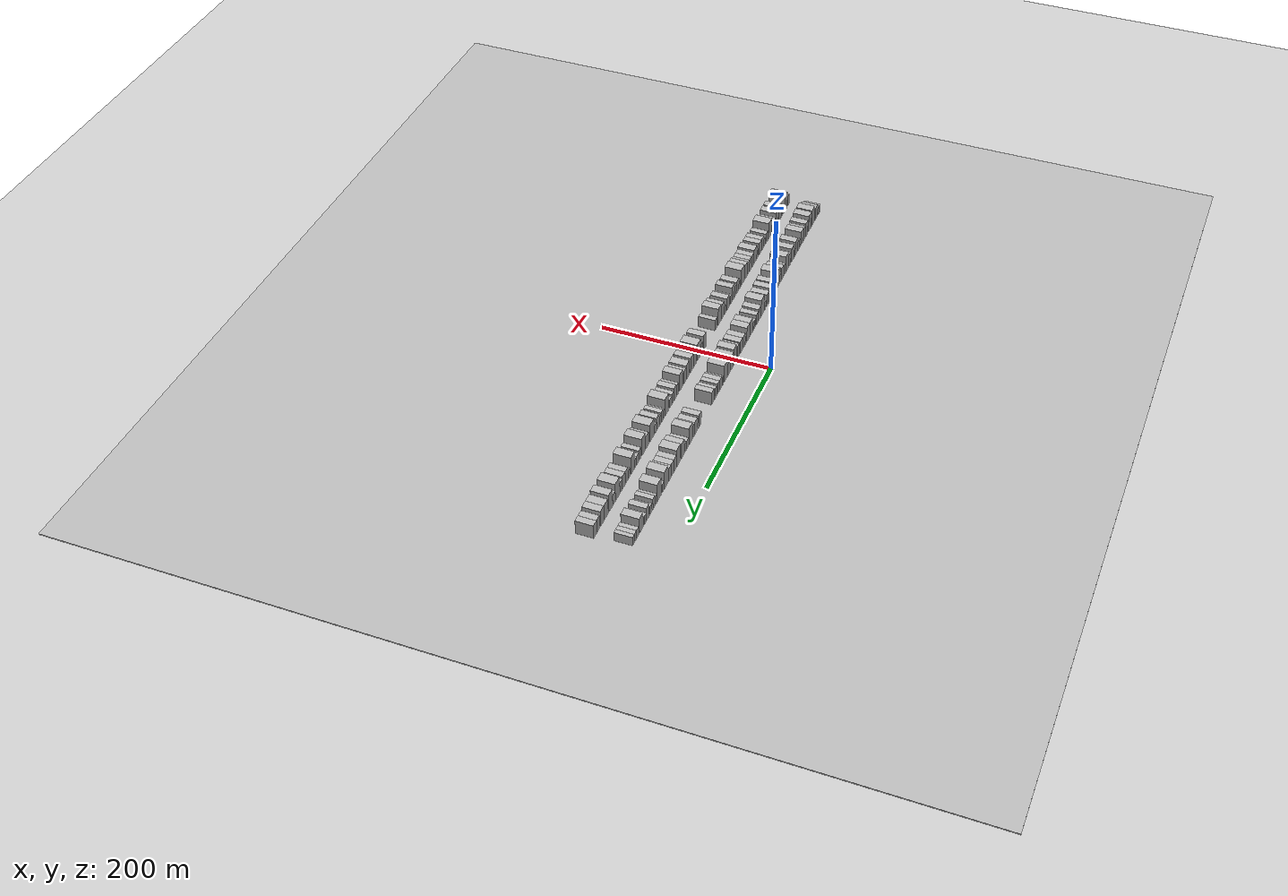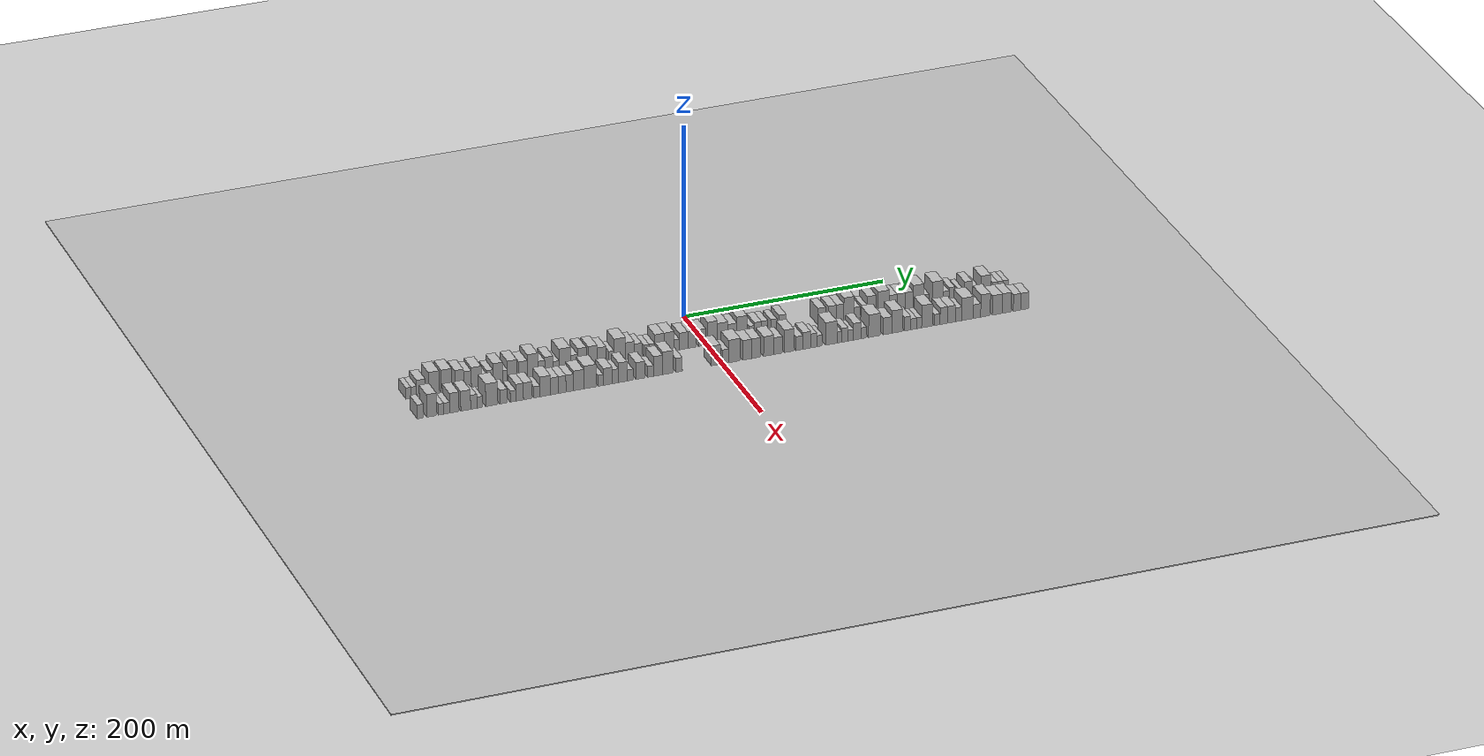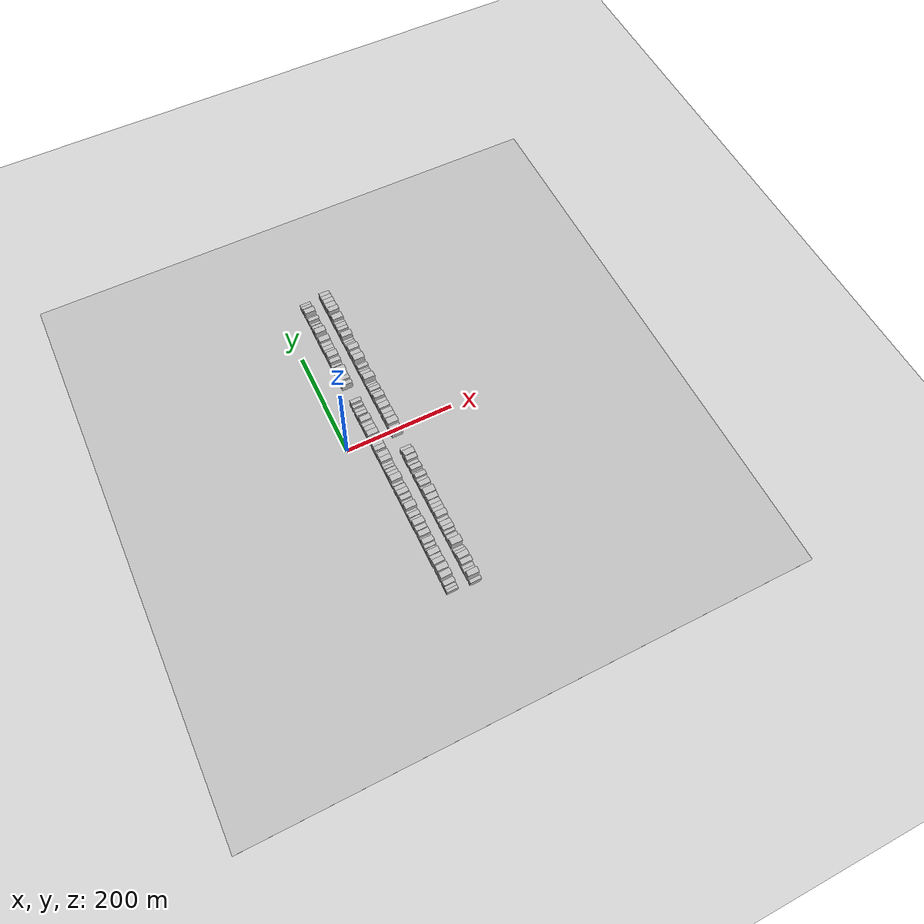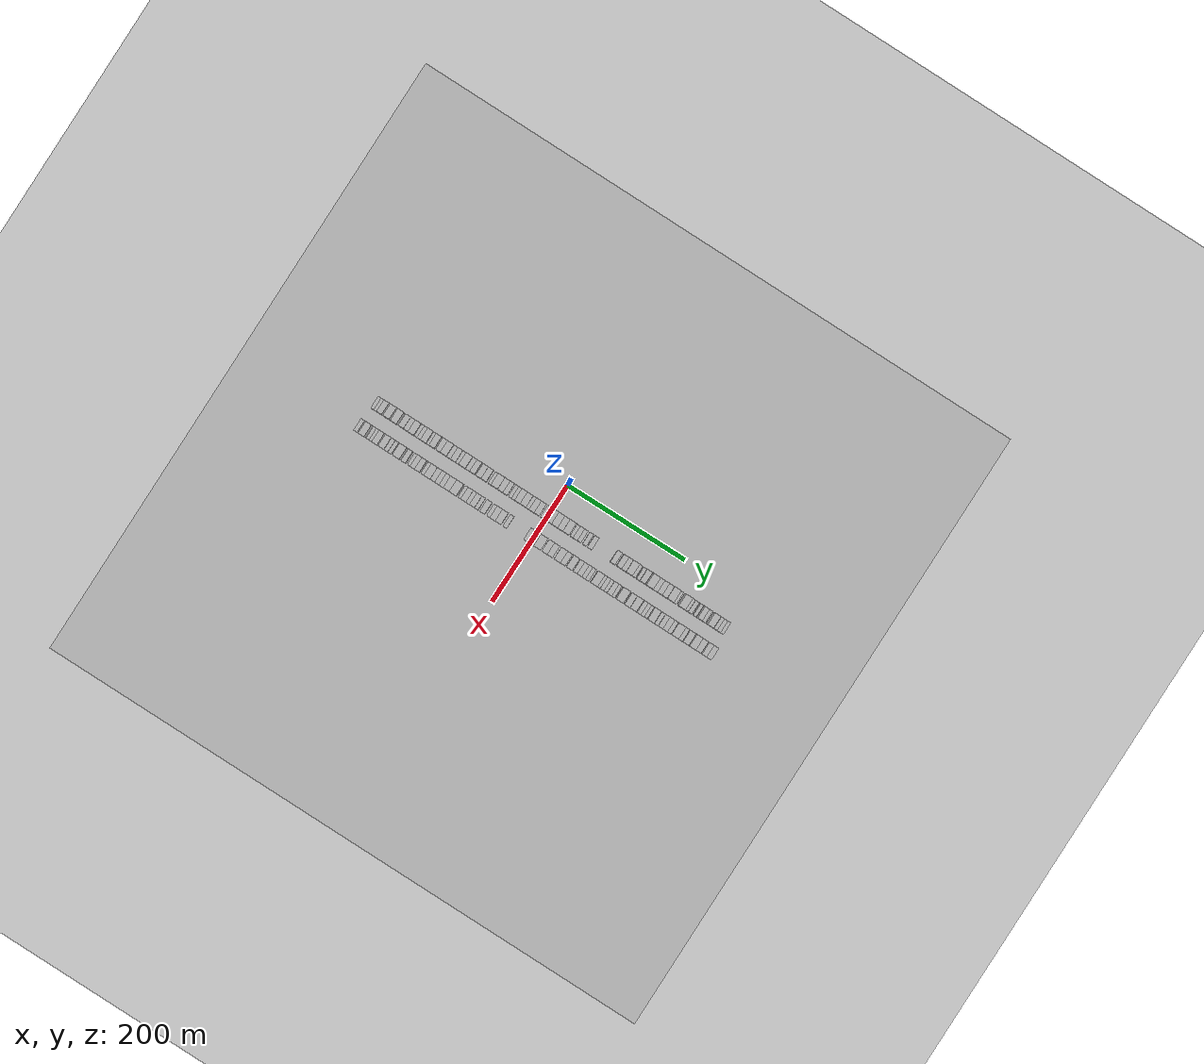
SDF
<?xml version="1.0" encoding="utf-8"?>

<sdf version="1.6">

   <world name="default">

      <gui fullscreen="0">

         <camera name="user_camera">

            <pose>-15 0 4.57585 0 0 0</pose>

            <view_controller>orbit</view_controller>

         </camera>

      </gui>

      <scene>

         <sky>

           <clouds>

             <speed>12</speed>

           </clouds>

         </sky>

         <ambient>0.4 0.4 0.4 1</ambient>

         <background>0.7 0.7 0.7 1</background>

         <shadows>1</shadows>

      </scene>

      <gravity>0 0 -9.8066</gravity>

      <magnetic_field>6e-06 2.3e-05 -4.2e-05</magnetic_field>

      <physics default="0" name="default_physics" type="ode">

         <ode>

            <solver>

               <type>quick</type>

               <iters>10</iters>

               <sor>1.0</sor>

               <use_dynamic_moi_rescaling>0</use_dynamic_moi_rescaling>

            </solver>

            <constraints>

               <cfm>0</cfm>

               <erp>0.2</erp>

               <contact_max_correcting_vel>100</contact_max_correcting_vel>

               <contact_surface_layer>0.001</contact_surface_layer>

            </constraints>

         </ode>

         <max_step_size>0.004</max_step_size>

         <real_time_factor>1</real_time_factor>

         <real_time_update_rate>250</real_time_update_rate>

      </physics>

      <light name="sun" type="directional">

         <cast_shadows>1</cast_shadows>

         <pose>0 0 10 0 0 0</pose>

         <diffuse>0.8 0.8 0.8 1</diffuse>

         <specular>0.2 0.2 0.2 1</specular>

         <attenuation>

            <range>1000</range>

            <constant>0.9</constant>

            <linear>0.01</linear>

            <quadratic>0.001</quadratic>

         </attenuation>

         <direction>-0.5 0.1 -0.9</direction>

      </light>

      <include>

         <name>ground_plane_1</name>

         <uri>model://HANNAS_ground_plane</uri>

         <pose>0 0 0  0 0 0</pose>

      </include>

      <include>

         <name>ground_plane_2</name>

         <uri>model://HANNAS_ground_plane</uri>

         <pose>100 0 0  0 0 0</pose>

      </include>

      <model name="building_1">

         <static>1</static>

         <pose frame="">50.0000 -294.4814 0 0.000000 0.000000 0.000000</pose>

         <link name="link">

            <pose frame="">0 0 6.00 0 0 0</pose>

            <collision name="collision">

               <geometry>

                  <box>

                     <size>20.0000 5.0373 12.0000</size>

                  </box>

               </geometry>

               <max_contacts>10</max_contacts>

               <surface>

                  <contact>

                     <ode/>

                  </contact>

                  <bounce/>

                  <friction>

                     <torsional>

                        <ode/>

                     </torsional>

                     <ode/>

                  </friction>

               </surface>

            </collision>

            <visual name="visual">

               <cast_shadows>0</cast_shadows>

               <geometry>

                  <box>

                     <size>20.0000 5.0373 12.0000</size>

                  </box>

               </geometry>

               <material>

                  <script>

                     <uri>model://HANNAS_wall/materials/scripts</uri>

                     <uri>model://HANNAS_wall/materials/textures</uri>

                     <name>vrc/HANNAS_wall</name>

                  </script>

               </material>

            </visual>

            <self_collide>0</self_collide>

            <enable_wind>0</enable_wind>

            <kinematic>0</kinematic>

         </link>

      </model>

      <model name="building_2">

         <static>1</static>

         <pose frame="">50.0000 -289.2743 0 0.000000 0.000000 0.000000</pose>

         <link name="link">

            <pose frame="">0 0 6.00 0 0 0</pose>

            <collision name="collision">

               <geometry>

                  <box>

                     <size>20.0000 5.3769 12.0000</size>

                  </box>

               </geometry>

               <max_contacts>10</max_contacts>

               <surface>

                  <contact>

                     <ode/>

                  </contact>

                  <bounce/>

                  <friction>

                     <torsional>

                        <ode/>

                     </torsional>

                     <ode/>

                  </friction>

               </surface>

            </collision>

            <visual name="visual">

               <cast_shadows>0</cast_shadows>

               <geometry>

                  <box>

                     <size>20.0000 5.3769 12.0000</size>

                  </box>

               </geometry>

               <material>

                  <script>

                     <uri>model://HANNAS_wall/materials/scripts</uri>

                     <uri>model://HANNAS_wall/materials/textures</uri>

                     <name>vrc/HANNAS_wall</name>

                  </script>

               </material>

            </visual>

            <self_collide>0</self_collide>

            <enable_wind>0</enable_wind>

            <kinematic>0</kinematic>

         </link>

      </model>

      <model name="building_3">

         <static>1</static>

         <pose frame="">50.0000 -282.2469 0 0.000000 0.000000 0.000000</pose>

         <link name="link">

            <pose frame="">0 0 9.00 0 0 0</pose>

            <collision name="collision">

               <geometry>

                  <box>

                     <size>20.0000 8.6779 18.0000</size>

                  </box>

               </geometry>

               <max_contacts>10</max_contacts>

               <surface>

                  <contact>

                     <ode/>

                  </contact>

                  <bounce/>

                  <friction>

                     <torsional>

                        <ode/>

                     </torsional>

                     <ode/>

                  </friction>

               </surface>

            </collision>

            <visual name="visual">

               <cast_shadows>0</cast_shadows>

               <geometry>

                  <box>

                     <size>20.0000 8.6779 18.0000</size>

                  </box>

               </geometry>

               <material>

                  <script>

                     <uri>model://HANNAS_wall/materials/scripts</uri>

                     <uri>model://HANNAS_wall/materials/textures</uri>

                     <name>vrc/HANNAS_wall</name>

                  </script>

               </material>

            </visual>

            <self_collide>0</self_collide>

            <enable_wind>0</enable_wind>

            <kinematic>0</kinematic>

         </link>

      </model>

      <model name="building_4">

         <static>1</static>

         <pose frame="">50.0000 -269.6992 0 0.000000 0.000000 0.000000</pose>

         <link name="link">

            <pose frame="">0 0 12.00 0 0 0</pose>

            <collision name="collision">

               <geometry>

                  <box>

                     <size>20.0000 10.4175 24.0000</size>

                  </box>

               </geometry>

               <max_contacts>10</max_contacts>

               <surface>

                  <contact>

                     <ode/>

                  </contact>

                  <bounce/>

                  <friction>

                     <torsional>

                        <ode/>

                     </torsional>

                     <ode/>

                  </friction>

               </surface>

            </collision>

            <visual name="visual">

               <cast_shadows>0</cast_shadows>

               <geometry>

                  <box>

                     <size>20.0000 10.4175 24.0000</size>

                  </box>

               </geometry>

               <material>

                  <script>

                     <uri>model://HANNAS_wall/materials/scripts</uri>

                     <uri>model://HANNAS_wall/materials/textures</uri>

                     <name>vrc/HANNAS_wall</name>

                  </script>

               </material>

            </visual>

            <self_collide>0</self_collide>

            <enable_wind>0</enable_wind>

            <kinematic>0</kinematic>

         </link>

      </model>

      <model name="building_5">

         <static>1</static>

         <pose frame="">50.0000 -257.3596 0 0.000000 0.000000 0.000000</pose>

         <link name="link">

            <pose frame="">0 0 12.00 0 0 0</pose>

            <collision name="collision">

               <geometry>

                  <box>

                     <size>20.0000 10.2619 24.0000</size>

                  </box>

               </geometry>

               <max_contacts>10</max_contacts>

               <surface>

                  <contact>

                     <ode/>

                  </contact>

                  <bounce/>

                  <friction>

                     <torsional>

                        <ode/>

                     </torsional>

                     <ode/>

                  </friction>

               </surface>

            </collision>

            <visual name="visual">

               <cast_shadows>0</cast_shadows>

               <geometry>

                  <box>

                     <size>20.0000 10.2619 24.0000</size>

                  </box>

               </geometry>

               <material>

                  <script>

                     <uri>model://HANNAS_wall/materials/scripts</uri>

                     <uri>model://HANNAS_wall/materials/textures</uri>

                     <name>vrc/HANNAS_wall</name>

                  </script>

               </material>

            </visual>

            <self_collide>0</self_collide>

            <enable_wind>0</enable_wind>

            <kinematic>0</kinematic>

         </link>

      </model>

      <model name="building_6">

         <static>1</static>

         <pose frame="">50.0000 -244.9306 0 0.000000 0.000000 0.000000</pose>

         <link name="link">

            <pose frame="">0 0 10.50 0 0 0</pose>

            <collision name="collision">

               <geometry>

                  <box>

                     <size>20.0000 8.5960 21.0000</size>

                  </box>

               </geometry>

               <max_contacts>10</max_contacts>

               <surface>

                  <contact>

                     <ode/>

                  </contact>

                  <bounce/>

                  <friction>

                     <torsional>

                        <ode/>

                     </torsional>

                     <ode/>

                  </friction>

               </surface>

            </collision>

            <visual name="visual">

               <cast_shadows>0</cast_shadows>

               <geometry>

                  <box>

                     <size>20.0000 8.5960 21.0000</size>

                  </box>

               </geometry>

               <material>

                  <script>

                     <uri>model://HANNAS_wall/materials/scripts</uri>

                     <uri>model://HANNAS_wall/materials/textures</uri>

                     <name>vrc/HANNAS_wall</name>

                  </script>

               </material>

            </visual>

            <self_collide>0</self_collide>

            <enable_wind>0</enable_wind>

            <kinematic>0</kinematic>

         </link>

      </model>

      <model name="building_7">

         <static>1</static>

         <pose frame="">50.0000 -236.8442 0 0.000000 0.000000 0.000000</pose>

         <link name="link">

            <pose frame="">0 0 9.00 0 0 0</pose>

            <collision name="collision">

               <geometry>

                  <box>

                     <size>20.0000 7.5769 18.0000</size>

                  </box>

               </geometry>

               <max_contacts>10</max_contacts>

               <surface>

                  <contact>

                     <ode/>

                  </contact>

                  <bounce/>

                  <friction>

                     <torsional>

                        <ode/>

                     </torsional>

                     <ode/>

                  </friction>

               </surface>

            </collision>

            <visual name="visual">

               <cast_shadows>0</cast_shadows>

               <geometry>

                  <box>

                     <size>20.0000 7.5769 18.0000</size>

                  </box>

               </geometry>

               <material>

                  <script>

                     <uri>model://HANNAS_wall/materials/scripts</uri>

                     <uri>model://HANNAS_wall/materials/textures</uri>

                     <name>vrc/HANNAS_wall</name>

                  </script>

               </material>

            </visual>

            <self_collide>0</self_collide>

            <enable_wind>0</enable_wind>

            <kinematic>0</kinematic>

         </link>

      </model>

      <model name="building_8">

         <static>1</static>

         <pose frame="">50.0000 -228.1408 0 0.000000 0.000000 0.000000</pose>

         <link name="link">

            <pose frame="">0 0 10.50 0 0 0</pose>

            <collision name="collision">

               <geometry>

                  <box>

                     <size>20.0000 9.8300 21.0000</size>

                  </box>

               </geometry>

               <max_contacts>10</max_contacts>

               <surface>

                  <contact>

                     <ode/>

                  </contact>

                  <bounce/>

                  <friction>

                     <torsional>

                        <ode/>

                     </torsional>

                     <ode/>

                  </friction>

               </surface>

            </collision>

            <visual name="visual">

               <cast_shadows>0</cast_shadows>

               <geometry>

                  <box>

                     <size>20.0000 9.8300 21.0000</size>

                  </box>

               </geometry>

               <material>

                  <script>

                     <uri>model://HANNAS_wall/materials/scripts</uri>

                     <uri>model://HANNAS_wall/materials/textures</uri>

                     <name>vrc/HANNAS_wall</name>

                  </script>

               </material>

            </visual>

            <self_collide>0</self_collide>

            <enable_wind>0</enable_wind>

            <kinematic>0</kinematic>

         </link>

      </model>

      <model name="building_9">

         <static>1</static>

         <pose frame="">50.0000 -220.6946 0 0.000000 0.000000 0.000000</pose>

         <link name="link">

            <pose frame="">0 0 6.00 0 0 0</pose>

            <collision name="collision">

               <geometry>

                  <box>

                     <size>20.0000 5.0625 12.0000</size>

                  </box>

               </geometry>

               <max_contacts>10</max_contacts>

               <surface>

                  <contact>

                     <ode/>

                  </contact>

                  <bounce/>

                  <friction>

                     <torsional>

                        <ode/>

                     </torsional>

                     <ode/>

                  </friction>

               </surface>

            </collision>

            <visual name="visual">

               <cast_shadows>0</cast_shadows>

               <geometry>

                  <box>

                     <size>20.0000 5.0625 12.0000</size>

                  </box>

               </geometry>

               <material>

                  <script>

                     <uri>model://HANNAS_wall/materials/scripts</uri>

                     <uri>model://HANNAS_wall/materials/textures</uri>

                     <name>vrc/HANNAS_wall</name>

                  </script>

               </material>

            </visual>

            <self_collide>0</self_collide>

            <enable_wind>0</enable_wind>

            <kinematic>0</kinematic>

         </link>

      </model>

      <model name="building_10">

         <static>1</static>

         <pose frame="">50.0000 -214.9720 0 0.000000 0.000000 0.000000</pose>

         <link name="link">

            <pose frame="">0 0 7.50 0 0 0</pose>

            <collision name="collision">

               <geometry>

                  <box>

                     <size>20.0000 6.3826 15.0000</size>

                  </box>

               </geometry>

               <max_contacts>10</max_contacts>

               <surface>

                  <contact>

                     <ode/>

                  </contact>

                  <bounce/>

                  <friction>

                     <torsional>

                        <ode/>

                     </torsional>

                     <ode/>

                  </friction>

               </surface>

            </collision>

            <visual name="visual">

               <cast_shadows>0</cast_shadows>

               <geometry>

                  <box>

                     <size>20.0000 6.3826 15.0000</size>

                  </box>

               </geometry>

               <material>

                  <script>

                     <uri>model://HANNAS_wall/materials/scripts</uri>

                     <uri>model://HANNAS_wall/materials/textures</uri>

                     <name>vrc/HANNAS_wall</name>

                  </script>

               </material>

            </visual>

            <self_collide>0</self_collide>

            <enable_wind>0</enable_wind>

            <kinematic>0</kinematic>

         </link>

      </model>

      <model name="building_11">

         <static>1</static>

         <pose frame="">50.0000 -207.1445 0 0.000000 0.000000 0.000000</pose>

         <link name="link">

            <pose frame="">0 0 10.50 0 0 0</pose>

            <collision name="collision">

               <geometry>

                  <box>

                     <size>20.0000 9.2723 21.0000</size>

                  </box>

               </geometry>

               <max_contacts>10</max_contacts>

               <surface>

                  <contact>

                     <ode/>

                  </contact>

                  <bounce/>

                  <friction>

                     <torsional>

                        <ode/>

                     </torsional>

                     <ode/>

                  </friction>

               </surface>

            </collision>

            <visual name="visual">

               <cast_shadows>0</cast_shadows>

               <geometry>

                  <box>

                     <size>20.0000 9.2723 21.0000</size>

                  </box>

               </geometry>

               <material>

                  <script>

                     <uri>model://HANNAS_wall/materials/scripts</uri>

                     <uri>model://HANNAS_wall/materials/textures</uri>

                     <name>vrc/HANNAS_wall</name>

                  </script>

               </material>

            </visual>

            <self_collide>0</self_collide>

            <enable_wind>0</enable_wind>

            <kinematic>0</kinematic>

         </link>

      </model>

      <model name="building_12">

         <static>1</static>

         <pose frame="">50.0000 -200.0656 0 0.000000 0.000000 0.000000</pose>

         <link name="link">

            <pose frame="">0 0 6.00 0 0 0</pose>

            <collision name="collision">

               <geometry>

                  <box>

                     <size>20.0000 4.8856 12.0000</size>

                  </box>

               </geometry>

               <max_contacts>10</max_contacts>

               <surface>

                  <contact>

                     <ode/>

                  </contact>

                  <bounce/>

                  <friction>

                     <torsional>

                        <ode/>

                     </torsional>

                     <ode/>

                  </friction>

               </surface>

            </collision>

            <visual name="visual">

               <cast_shadows>0</cast_shadows>

               <geometry>

                  <box>

                     <size>20.0000 4.8856 12.0000</size>

                  </box>

               </geometry>

               <material>

                  <script>

                     <uri>model://HANNAS_wall/materials/scripts</uri>

                     <uri>model://HANNAS_wall/materials/textures</uri>

                     <name>vrc/HANNAS_wall</name>

                  </script>

               </material>

            </visual>

            <self_collide>0</self_collide>

            <enable_wind>0</enable_wind>

            <kinematic>0</kinematic>

         </link>

      </model>

      <model name="building_13">

         <static>1</static>

         <pose frame="">50.0000 -192.9678 0 0.000000 0.000000 0.000000</pose>

         <link name="link">

            <pose frame="">0 0 10.50 0 0 0</pose>

            <collision name="collision">

               <geometry>

                  <box>

                     <size>20.0000 9.3100 21.0000</size>

                  </box>

               </geometry>

               <max_contacts>10</max_contacts>

               <surface>

                  <contact>

                     <ode/>

                  </contact>

                  <bounce/>

                  <friction>

                     <torsional>

                        <ode/>

                     </torsional>

                     <ode/>

                  </friction>

               </surface>

            </collision>

            <visual name="visual">

               <cast_shadows>0</cast_shadows>

               <geometry>

                  <box>

                     <size>20.0000 9.3100 21.0000</size>

                  </box>

               </geometry>

               <material>

                  <script>

                     <uri>model://HANNAS_wall/materials/scripts</uri>

                     <uri>model://HANNAS_wall/materials/textures</uri>

                     <name>vrc/HANNAS_wall</name>

                  </script>

               </material>

            </visual>

            <self_collide>0</self_collide>

            <enable_wind>0</enable_wind>

            <kinematic>0</kinematic>

         </link>

      </model>

      <model name="building_14">

         <static>1</static>

         <pose frame="">50.0000 -182.2153 0 0.000000 0.000000 0.000000</pose>

         <link name="link">

            <pose frame="">0 0 9.00 0 0 0</pose>

            <collision name="collision">

               <geometry>

                  <box>

                     <size>20.0000 8.1949 18.0000</size>

                  </box>

               </geometry>

               <max_contacts>10</max_contacts>

               <surface>

                  <contact>

                     <ode/>

                  </contact>

                  <bounce/>

                  <friction>

                     <torsional>

                        <ode/>

                     </torsional>

                     <ode/>

                  </friction>

               </surface>

            </collision>

            <visual name="visual">

               <cast_shadows>0</cast_shadows>

               <geometry>

                  <box>

                     <size>20.0000 8.1949 18.0000</size>

                  </box>

               </geometry>

               <material>

                  <script>

                     <uri>model://HANNAS_wall/materials/scripts</uri>

                     <uri>model://HANNAS_wall/materials/textures</uri>

                     <name>vrc/HANNAS_wall</name>

                  </script>

               </material>

            </visual>

            <self_collide>0</self_collide>

            <enable_wind>0</enable_wind>

            <kinematic>0</kinematic>

         </link>

      </model>

      <model name="building_15">

         <static>1</static>

         <pose frame="">50.0000 -172.9326 0 0.000000 0.000000 0.000000</pose>

         <link name="link">

            <pose frame="">0 0 12.00 0 0 0</pose>

            <collision name="collision">

               <geometry>

                  <box>

                     <size>20.0000 10.3706 24.0000</size>

                  </box>

               </geometry>

               <max_contacts>10</max_contacts>

               <surface>

                  <contact>

                     <ode/>

                  </contact>

                  <bounce/>

                  <friction>

                     <torsional>

                        <ode/>

                     </torsional>

                     <ode/>

                  </friction>

               </surface>

            </collision>

            <visual name="visual">

               <cast_shadows>0</cast_shadows>

               <geometry>

                  <box>

                     <size>20.0000 10.3706 24.0000</size>

                  </box>

               </geometry>

               <material>

                  <script>

                     <uri>model://HANNAS_wall/materials/scripts</uri>

                     <uri>model://HANNAS_wall/materials/textures</uri>

                     <name>vrc/HANNAS_wall</name>

                  </script>

               </material>

            </visual>

            <self_collide>0</self_collide>

            <enable_wind>0</enable_wind>

            <kinematic>0</kinematic>

         </link>

      </model>

      <model name="building_16">

         <static>1</static>

         <pose frame="">50.0000 -164.3762 0 0.000000 0.000000 0.000000</pose>

         <link name="link">

            <pose frame="">0 0 7.50 0 0 0</pose>

            <collision name="collision">

               <geometry>

                  <box>

                     <size>20.0000 6.7421 15.0000</size>

                  </box>

               </geometry>

               <max_contacts>10</max_contacts>

               <surface>

                  <contact>

                     <ode/>

                  </contact>

                  <bounce/>

                  <friction>

                     <torsional>

                        <ode/>

                     </torsional>

                     <ode/>

                  </friction>

               </surface>

            </collision>

            <visual name="visual">

               <cast_shadows>0</cast_shadows>

               <geometry>

                  <box>

                     <size>20.0000 6.7421 15.0000</size>

                  </box>

               </geometry>

               <material>

                  <script>

                     <uri>model://HANNAS_wall/materials/scripts</uri>

                     <uri>model://HANNAS_wall/materials/textures</uri>

                     <name>vrc/HANNAS_wall</name>

                  </script>

               </material>

            </visual>

            <self_collide>0</self_collide>

            <enable_wind>0</enable_wind>

            <kinematic>0</kinematic>

         </link>

      </model>

      <model name="building_17">

         <static>1</static>

         <pose frame="">50.0000 -156.8604 0 0.000000 0.000000 0.000000</pose>

         <link name="link">

            <pose frame="">0 0 9.00 0 0 0</pose>

            <collision name="collision">

               <geometry>

                  <box>

                     <size>20.0000 8.2895 18.0000</size>

                  </box>

               </geometry>

               <max_contacts>10</max_contacts>

               <surface>

                  <contact>

                     <ode/>

                  </contact>

                  <bounce/>

                  <friction>

                     <torsional>

                        <ode/>

                     </torsional>

                     <ode/>

                  </friction>

               </surface>

            </collision>

            <visual name="visual">

               <cast_shadows>0</cast_shadows>

               <geometry>

                  <box>

                     <size>20.0000 8.2895 18.0000</size>

                  </box>

               </geometry>

               <material>

                  <script>

                     <uri>model://HANNAS_wall/materials/scripts</uri>

                     <uri>model://HANNAS_wall/materials/textures</uri>

                     <name>vrc/HANNAS_wall</name>

                  </script>

               </material>

            </visual>

            <self_collide>0</self_collide>

            <enable_wind>0</enable_wind>

            <kinematic>0</kinematic>

         </link>

      </model>

      <model name="building_18">

         <static>1</static>

         <pose frame="">50.0000 -149.8223 0 0.000000 0.000000 0.000000</pose>

         <link name="link">

            <pose frame="">0 0 6.00 0 0 0</pose>

            <collision name="collision">

               <geometry>

                  <box>

                     <size>20.0000 5.7867 12.0000</size>

                  </box>

               </geometry>

               <max_contacts>10</max_contacts>

               <surface>

                  <contact>

                     <ode/>

                  </contact>

                  <bounce/>

                  <friction>

                     <torsional>

                        <ode/>

                     </torsional>

                     <ode/>

                  </friction>

               </surface>

            </collision>

            <visual name="visual">

               <cast_shadows>0</cast_shadows>

               <geometry>

                  <box>

                     <size>20.0000 5.7867 12.0000</size>

                  </box>

               </geometry>

               <material>

                  <script>

                     <uri>model://HANNAS_wall/materials/scripts</uri>

                     <uri>model://HANNAS_wall/materials/textures</uri>

                     <name>vrc/HANNAS_wall</name>

                  </script>

               </material>

            </visual>

            <self_collide>0</self_collide>

            <enable_wind>0</enable_wind>

            <kinematic>0</kinematic>

         </link>

      </model>

      <model name="building_19">

         <static>1</static>

         <pose frame="">50.0000 -141.2741 0 0.000000 0.000000 0.000000</pose>

         <link name="link">

            <pose frame="">0 0 12.00 0 0 0</pose>

            <collision name="collision">

               <geometry>

                  <box>

                     <size>20.0000 11.3098 24.0000</size>

                  </box>

               </geometry>

               <max_contacts>10</max_contacts>

               <surface>

                  <contact>

                     <ode/>

                  </contact>

                  <bounce/>

                  <friction>

                     <torsional>

                        <ode/>

                     </torsional>

                     <ode/>

                  </friction>

               </surface>

            </collision>

            <visual name="visual">

               <cast_shadows>0</cast_shadows>

               <geometry>

                  <box>

                     <size>20.0000 11.3098 24.0000</size>

                  </box>

               </geometry>

               <material>

                  <script>

                     <uri>model://HANNAS_wall/materials/scripts</uri>

                     <uri>model://HANNAS_wall/materials/textures</uri>

                     <name>vrc/HANNAS_wall</name>

                  </script>

               </material>

            </visual>

            <self_collide>0</self_collide>

            <enable_wind>0</enable_wind>

            <kinematic>0</kinematic>

         </link>

      </model>

      <model name="building_20">

         <static>1</static>

         <pose frame="">50.0000 -132.0643 0 0.000000 0.000000 0.000000</pose>

         <link name="link">

            <pose frame="">0 0 7.50 0 0 0</pose>

            <collision name="collision">

               <geometry>

                  <box>

                     <size>20.0000 7.1097 15.0000</size>

                  </box>

               </geometry>

               <max_contacts>10</max_contacts>

               <surface>

                  <contact>

                     <ode/>

                  </contact>

                  <bounce/>

                  <friction>

                     <torsional>

                        <ode/>

                     </torsional>

                     <ode/>

                  </friction>

               </surface>

            </collision>

            <visual name="visual">

               <cast_shadows>0</cast_shadows>

               <geometry>

                  <box>

                     <size>20.0000 7.1097 15.0000</size>

                  </box>

               </geometry>

               <material>

                  <script>

                     <uri>model://HANNAS_wall/materials/scripts</uri>

                     <uri>model://HANNAS_wall/materials/textures</uri>

                     <name>vrc/HANNAS_wall</name>

                  </script>

               </material>

            </visual>

            <self_collide>0</self_collide>

            <enable_wind>0</enable_wind>

            <kinematic>0</kinematic>

         </link>

      </model>

      <model name="building_21">

         <static>1</static>

         <pose frame="">50.0000 -124.2901 0 0.000000 0.000000 0.000000</pose>

         <link name="link">

            <pose frame="">0 0 10.50 0 0 0</pose>

            <collision name="collision">

               <geometry>

                  <box>

                     <size>20.0000 8.4387 21.0000</size>

                  </box>

               </geometry>

               <max_contacts>10</max_contacts>

               <surface>

                  <contact>

                     <ode/>

                  </contact>

                  <bounce/>

                  <friction>

                     <torsional>

                        <ode/>

                     </torsional>

                     <ode/>

                  </friction>

               </surface>

            </collision>

            <visual name="visual">

               <cast_shadows>0</cast_shadows>

               <geometry>

                  <box>

                     <size>20.0000 8.4387 21.0000</size>

                  </box>

               </geometry>

               <material>

                  <script>

                     <uri>model://HANNAS_wall/materials/scripts</uri>

                     <uri>model://HANNAS_wall/materials/textures</uri>

                     <name>vrc/HANNAS_wall</name>

                  </script>

               </material>

            </visual>

            <self_collide>0</self_collide>

            <enable_wind>0</enable_wind>

            <kinematic>0</kinematic>

         </link>

      </model>

      <model name="building_22">

         <static>1</static>

         <pose frame="">50.0000 -113.6414 0 0.000000 0.000000 0.000000</pose>

         <link name="link">

            <pose frame="">0 0 10.50 0 0 0</pose>

            <collision name="collision">

               <geometry>

                  <box>

                     <size>20.0000 8.8589 21.0000</size>

                  </box>

               </geometry>

               <max_contacts>10</max_contacts>

               <surface>

                  <contact>

                     <ode/>

                  </contact>

                  <bounce/>

                  <friction>

                     <torsional>

                        <ode/>

                     </torsional>

                     <ode/>

                  </friction>

               </surface>

            </collision>

            <visual name="visual">

               <cast_shadows>0</cast_shadows>

               <geometry>

                  <box>

                     <size>20.0000 8.8589 21.0000</size>

                  </box>

               </geometry>

               <material>

                  <script>

                     <uri>model://HANNAS_wall/materials/scripts</uri>

                     <uri>model://HANNAS_wall/materials/textures</uri>

                     <name>vrc/HANNAS_wall</name>

                  </script>

               </material>

            </visual>

            <self_collide>0</self_collide>

            <enable_wind>0</enable_wind>

            <kinematic>0</kinematic>

         </link>

      </model>

      <model name="building_23">

         <static>1</static>

         <pose frame="">50.0000 -104.8949 0 0.000000 0.000000 0.000000</pose>

         <link name="link">

            <pose frame="">0 0 9.00 0 0 0</pose>

            <collision name="collision">

               <geometry>

                  <box>

                     <size>20.0000 8.6341 18.0000</size>

                  </box>

               </geometry>

               <max_contacts>10</max_contacts>

               <surface>

                  <contact>

                     <ode/>

                  </contact>

                  <bounce/>

                  <friction>

                     <torsional>

                        <ode/>

                     </torsional>

                     <ode/>

                  </friction>

               </surface>

            </collision>

            <visual name="visual">

               <cast_shadows>0</cast_shadows>

               <geometry>

                  <box>

                     <size>20.0000 8.6341 18.0000</size>

                  </box>

               </geometry>

               <material>

                  <script>

                     <uri>model://HANNAS_wall/materials/scripts</uri>

                     <uri>model://HANNAS_wall/materials/textures</uri>

                     <name>vrc/HANNAS_wall</name>

                  </script>

               </material>

            </visual>

            <self_collide>0</self_collide>

            <enable_wind>0</enable_wind>

            <kinematic>0</kinematic>

         </link>

      </model>

      <model name="building_24">

         <static>1</static>

         <pose frame="">50.0000 -95.0213 0 0.000000 0.000000 0.000000</pose>

         <link name="link">

            <pose frame="">0 0 6.00 0 0 0</pose>

            <collision name="collision">

               <geometry>

                  <box>

                     <size>20.0000 5.1131 12.0000</size>

                  </box>

               </geometry>

               <max_contacts>10</max_contacts>

               <surface>

                  <contact>

                     <ode/>

                  </contact>

                  <bounce/>

                  <friction>

                     <torsional>

                        <ode/>

                     </torsional>

                     <ode/>

                  </friction>

               </surface>

            </collision>

            <visual name="visual">

               <cast_shadows>0</cast_shadows>

               <geometry>

                  <box>

                     <size>20.0000 5.1131 12.0000</size>

                  </box>

               </geometry>

               <material>

                  <script>

                     <uri>model://HANNAS_wall/materials/scripts</uri>

                     <uri>model://HANNAS_wall/materials/textures</uri>

                     <name>vrc/HANNAS_wall</name>

                  </script>

               </material>

            </visual>

            <self_collide>0</self_collide>

            <enable_wind>0</enable_wind>

            <kinematic>0</kinematic>

         </link>

      </model>

      <model name="building_25">

         <static>1</static>

         <pose frame="">50.0000 -86.7722 0 0.000000 0.000000 0.000000</pose>

         <link name="link">

            <pose frame="">0 0 12.00 0 0 0</pose>

            <collision name="collision">

               <geometry>

                  <box>

                     <size>20.0000 11.3852 24.0000</size>

                  </box>

               </geometry>

               <max_contacts>10</max_contacts>

               <surface>

                  <contact>

                     <ode/>

                  </contact>

                  <bounce/>

                  <friction>

                     <torsional>

                        <ode/>

                     </torsional>

                     <ode/>

                  </friction>

               </surface>

            </collision>

            <visual name="visual">

               <cast_shadows>0</cast_shadows>

               <geometry>

                  <box>

                     <size>20.0000 11.3852 24.0000</size>

                  </box>

               </geometry>

               <material>

                  <script>

                     <uri>model://HANNAS_wall/materials/scripts</uri>

                     <uri>model://HANNAS_wall/materials/textures</uri>

                     <name>vrc/HANNAS_wall</name>

                  </script>

               </material>

            </visual>

            <self_collide>0</self_collide>

            <enable_wind>0</enable_wind>

            <kinematic>0</kinematic>

         </link>

      </model>

      <model name="building_26">

         <static>1</static>

         <pose frame="">50.0000 -76.6967 0 0.000000 0.000000 0.000000</pose>

         <link name="link">

            <pose frame="">0 0 9.00 0 0 0</pose>

            <collision name="collision">

               <geometry>

                  <box>

                     <size>20.0000 8.7659 18.0000</size>

                  </box>

               </geometry>

               <max_contacts>10</max_contacts>

               <surface>

                  <contact>

                     <ode/>

                  </contact>

                  <bounce/>

                  <friction>

                     <torsional>

                        <ode/>

                     </torsional>

                     <ode/>

                  </friction>

               </surface>

            </collision>

            <visual name="visual">

               <cast_shadows>0</cast_shadows>

               <geometry>

                  <box>

                     <size>20.0000 8.7659 18.0000</size>

                  </box>

               </geometry>

               <material>

                  <script>

                     <uri>model://HANNAS_wall/materials/scripts</uri>

                     <uri>model://HANNAS_wall/materials/textures</uri>

                     <name>vrc/HANNAS_wall</name>

                  </script>

               </material>

            </visual>

            <self_collide>0</self_collide>

            <enable_wind>0</enable_wind>

            <kinematic>0</kinematic>

         </link>

      </model>

      <model name="building_27">

         <static>1</static>

         <pose frame="">50.0000 -68.6961 0 0.000000 0.000000 0.000000</pose>

         <link name="link">

            <pose frame="">0 0 7.50 0 0 0</pose>

            <collision name="collision">

               <geometry>

                  <box>

                     <size>20.0000 7.2352 15.0000</size>

                  </box>

               </geometry>

               <max_contacts>10</max_contacts>

               <surface>

                  <contact>

                     <ode/>

                  </contact>

                  <bounce/>

                  <friction>

                     <torsional>

                        <ode/>

                     </torsional>

                     <ode/>

                  </friction>

               </surface>

            </collision>

            <visual name="visual">

               <cast_shadows>0</cast_shadows>

               <geometry>

                  <box>

                     <size>20.0000 7.2352 15.0000</size>

                  </box>

               </geometry>

               <material>

                  <script>

                     <uri>model://HANNAS_wall/materials/scripts</uri>

                     <uri>model://HANNAS_wall/materials/textures</uri>

                     <name>vrc/HANNAS_wall</name>

                  </script>

               </material>

            </visual>

            <self_collide>0</self_collide>

            <enable_wind>0</enable_wind>

            <kinematic>0</kinematic>

         </link>

      </model>

      <model name="building_28">

         <static>1</static>

         <pose frame="">50.0000 -60.4429 0 0.000000 0.000000 0.000000</pose>

         <link name="link">

            <pose frame="">0 0 6.00 0 0 0</pose>

            <collision name="collision">

               <geometry>

                  <box>

                     <size>20.0000 5.2712 12.0000</size>

                  </box>

               </geometry>

               <max_contacts>10</max_contacts>

               <surface>

                  <contact>

                     <ode/>

                  </contact>

                  <bounce/>

                  <friction>

                     <torsional>

                        <ode/>

                     </torsional>

                     <ode/>

                  </friction>

               </surface>

            </collision>

            <visual name="visual">

               <cast_shadows>0</cast_shadows>

               <geometry>

                  <box>

                     <size>20.0000 5.2712 12.0000</size>

                  </box>

               </geometry>

               <material>

                  <script>

                     <uri>model://HANNAS_wall/materials/scripts</uri>

                     <uri>model://HANNAS_wall/materials/textures</uri>

                     <name>vrc/HANNAS_wall</name>

                  </script>

               </material>

            </visual>

            <self_collide>0</self_collide>

            <enable_wind>0</enable_wind>

            <kinematic>0</kinematic>

         </link>

      </model>

      <model name="building_29">

         <static>1</static>

         <pose frame="">50.0000 -55.0356 0 0.000000 0.000000 0.000000</pose>

         <link name="link">

            <pose frame="">0 0 6.00 0 0 0</pose>

            <collision name="collision">

               <geometry>

                  <box>

                     <size>20.0000 5.5434 12.0000</size>

                  </box>

               </geometry>

               <max_contacts>10</max_contacts>

               <surface>

                  <contact>

                     <ode/>

                  </contact>

                  <bounce/>

                  <friction>

                     <torsional>

                        <ode/>

                     </torsional>

                     <ode/>

                  </friction>

               </surface>

            </collision>

            <visual name="visual">

               <cast_shadows>0</cast_shadows>

               <geometry>

                  <box>

                     <size>20.0000 5.5434 12.0000</size>

                  </box>

               </geometry>

               <material>

                  <script>

                     <uri>model://HANNAS_wall/materials/scripts</uri>

                     <uri>model://HANNAS_wall/materials/textures</uri>

                     <name>vrc/HANNAS_wall</name>

                  </script>

               </material>

            </visual>

            <self_collide>0</self_collide>

            <enable_wind>0</enable_wind>

            <kinematic>0</kinematic>

         </link>

      </model>

      <model name="building_30">

         <static>1</static>

         <pose frame="">50.0000 -47.6244 0 0.000000 0.000000 0.000000</pose>

         <link name="link">

            <pose frame="">0 0 10.50 0 0 0</pose>

            <collision name="collision">

               <geometry>

                  <box>

                     <size>20.0000 9.2790 21.0000</size>

                  </box>

               </geometry>

               <max_contacts>10</max_contacts>

               <surface>

                  <contact>

                     <ode/>

                  </contact>

                  <bounce/>

                  <friction>

                     <torsional>

                        <ode/>

                     </torsional>

                     <ode/>

                  </friction>

               </surface>

            </collision>

            <visual name="visual">

               <cast_shadows>0</cast_shadows>

               <geometry>

                  <box>

                     <size>20.0000 9.2790 21.0000</size>

                  </box>

               </geometry>

               <material>

                  <script>

                     <uri>model://HANNAS_wall/materials/scripts</uri>

                     <uri>model://HANNAS_wall/materials/textures</uri>

                     <name>vrc/HANNAS_wall</name>

                  </script>

               </material>

            </visual>

            <self_collide>0</self_collide>

            <enable_wind>0</enable_wind>

            <kinematic>0</kinematic>

         </link>

      </model>

      <model name="building_31">

         <static>1</static>

         <pose frame="">50.0000 -38.0883 0 0.000000 0.000000 0.000000</pose>

         <link name="link">

            <pose frame="">0 0 10.50 0 0 0</pose>

            <collision name="collision">

               <geometry>

                  <box>

                     <size>20.0000 9.7932 21.0000</size>

                  </box>

               </geometry>

               <max_contacts>10</max_contacts>

               <surface>

                  <contact>

                     <ode/>

                  </contact>

                  <bounce/>

                  <friction>

                     <torsional>

                        <ode/>

                     </torsional>

                     <ode/>

                  </friction>

               </surface>

            </collision>

            <visual name="visual">

               <cast_shadows>0</cast_shadows>

               <geometry>

                  <box>

                     <size>20.0000 9.7932 21.0000</size>

                  </box>

               </geometry>

               <material>

                  <script>

                     <uri>model://HANNAS_wall/materials/scripts</uri>

                     <uri>model://HANNAS_wall/materials/textures</uri>

                     <name>vrc/HANNAS_wall</name>

                  </script>

               </material>

            </visual>

            <self_collide>0</self_collide>

            <enable_wind>0</enable_wind>

            <kinematic>0</kinematic>

         </link>

      </model>

      <model name="building_32">

         <static>1</static>

         <pose frame="">50.0000 -30.5219 0 0.000000 0.000000 0.000000</pose>

         <link name="link">

            <pose frame="">0 0 6.00 0 0 0</pose>

            <collision name="collision">

               <geometry>

                  <box>

                     <size>20.0000 5.3396 12.0000</size>

                  </box>

               </geometry>

               <max_contacts>10</max_contacts>

               <surface>

                  <contact>

                     <ode/>

                  </contact>

                  <bounce/>

                  <friction>

                     <torsional>

                        <ode/>

                     </torsional>

                     <ode/>

                  </friction>

               </surface>

            </collision>

            <visual name="visual">

               <cast_shadows>0</cast_shadows>

               <geometry>

                  <box>

                     <size>20.0000 5.3396 12.0000</size>

                  </box>

               </geometry>

               <material>

                  <script>

                     <uri>model://HANNAS_wall/materials/scripts</uri>

                     <uri>model://HANNAS_wall/materials/textures</uri>

                     <name>vrc/HANNAS_wall</name>

                  </script>

               </material>

            </visual>

            <self_collide>0</self_collide>

            <enable_wind>0</enable_wind>

            <kinematic>0</kinematic>

         </link>

      </model>

      <model name="building_33">

         <static>1</static>

         <pose frame="">50.0000 -23.6054 0 0.000000 0.000000 0.000000</pose>

         <link name="link">

            <pose frame="">0 0 9.00 0 0 0</pose>

            <collision name="collision">

               <geometry>

                  <box>

                     <size>20.0000 8.4933 18.0000</size>

                  </box>

               </geometry>

               <max_contacts>10</max_contacts>

               <surface>

                  <contact>

                     <ode/>

                  </contact>

                  <bounce/>

                  <friction>

                     <torsional>

                        <ode/>

                     </torsional>

                     <ode/>

                  </friction>

               </surface>

            </collision>

            <visual name="visual">

               <cast_shadows>0</cast_shadows>

               <geometry>

                  <box>

                     <size>20.0000 8.4933 18.0000</size>

                  </box>

               </geometry>

               <material>

                  <script>

                     <uri>model://HANNAS_wall/materials/scripts</uri>

                     <uri>model://HANNAS_wall/materials/textures</uri>

                     <name>vrc/HANNAS_wall</name>

                  </script>

               </material>

            </visual>

            <self_collide>0</self_collide>

            <enable_wind>0</enable_wind>

            <kinematic>0</kinematic>

         </link>

      </model>

      <model name="building_34">

         <static>1</static>

         <pose frame="">50.0000 -15.1168 0 0.000000 0.000000 0.000000</pose>

         <link name="link">

            <pose frame="">0 0 9.00 0 0 0</pose>

            <collision name="collision">

               <geometry>

                  <box>

                     <size>20.0000 8.4840 18.0000</size>

                  </box>

               </geometry>

               <max_contacts>10</max_contacts>

               <surface>

                  <contact>

                     <ode/>

                  </contact>

                  <bounce/>

                  <friction>

                     <torsional>

                        <ode/>

                     </torsional>

                     <ode/>

                  </friction>

               </surface>

            </collision>

            <visual name="visual">

               <cast_shadows>0</cast_shadows>

               <geometry>

                  <box>

                     <size>20.0000 8.4840 18.0000</size>

                  </box>

               </geometry>

               <material>

                  <script>

                     <uri>model://HANNAS_wall/materials/scripts</uri>

                     <uri>model://HANNAS_wall/materials/textures</uri>

                     <name>vrc/HANNAS_wall</name>

                  </script>

               </material>

            </visual>

            <self_collide>0</self_collide>

            <enable_wind>0</enable_wind>

            <kinematic>0</kinematic>

         </link>

      </model>

      <model name="building_35">

         <static>1</static>

         <pose frame="">50.0000 -5.2553 0 0.000000 0.000000 0.000000</pose>

         <link name="link">

            <pose frame="">0 0 9.00 0 0 0</pose>

            <collision name="collision">

               <geometry>

                  <box>

                     <size>20.0000 7.2390 18.0000</size>

                  </box>

               </geometry>

               <max_contacts>10</max_contacts>

               <surface>

                  <contact>

                     <ode/>

                  </contact>

                  <bounce/>

                  <friction>

                     <torsional>

                        <ode/>

                     </torsional>

                     <ode/>

                  </friction>

               </surface>

            </collision>

            <visual name="visual">

               <cast_shadows>0</cast_shadows>

               <geometry>

                  <box>

                     <size>20.0000 7.2390 18.0000</size>

                  </box>

               </geometry>

               <material>

                  <script>

                     <uri>model://HANNAS_wall/materials/scripts</uri>

                     <uri>model://HANNAS_wall/materials/textures</uri>

                     <name>vrc/HANNAS_wall</name>

                  </script>

               </material>

            </visual>

            <self_collide>0</self_collide>

            <enable_wind>0</enable_wind>

            <kinematic>0</kinematic>

         </link>

      </model>

      <model name="building_36">

         <static>1</static>

         <pose frame="">50.0000 5.2989 0 0.000000 0.000000 0.000000</pose>

         <link name="link">

            <pose frame="">0 0 12.00 0 0 0</pose>

            <collision name="collision">

               <geometry>

                  <box>

                     <size>20.0000 9.8693 24.0000</size>

                  </box>

               </geometry>

               <max_contacts>10</max_contacts>

               <surface>

                  <contact>

                     <ode/>

                  </contact>

                  <bounce/>

                  <friction>

                     <torsional>

                        <ode/>

                     </torsional>

                     <ode/>

                  </friction>

               </surface>

            </collision>

            <visual name="visual">

               <cast_shadows>0</cast_shadows>

               <geometry>

                  <box>

                     <size>20.0000 9.8693 24.0000</size>

                  </box>

               </geometry>

               <material>

                  <script>

                     <uri>model://HANNAS_wall/materials/scripts</uri>

                     <uri>model://HANNAS_wall/materials/textures</uri>

                     <name>vrc/HANNAS_wall</name>

                  </script>

               </material>

            </visual>

            <self_collide>0</self_collide>

            <enable_wind>0</enable_wind>

            <kinematic>0</kinematic>

         </link>

      </model>

      <model name="building_37">

         <static>1</static>

         <pose frame="">50.0000 15.3436 0 0.000000 0.000000 0.000000</pose>

         <link name="link">

            <pose frame="">0 0 10.50 0 0 0</pose>

            <collision name="collision">

               <geometry>

                  <box>

                     <size>20.0000 10.2202 21.0000</size>

                  </box>

               </geometry>

               <max_contacts>10</max_contacts>

               <surface>

                  <contact>

                     <ode/>

                  </contact>

                  <bounce/>

                  <friction>

                     <torsional>

                        <ode/>

                     </torsional>

                     <ode/>

                  </friction>

               </surface>

            </collision>

            <visual name="visual">

               <cast_shadows>0</cast_shadows>

               <geometry>

                  <box>

                     <size>20.0000 10.2202 21.0000</size>

                  </box>

               </geometry>

               <material>

                  <script>

                     <uri>model://HANNAS_wall/materials/scripts</uri>

                     <uri>model://HANNAS_wall/materials/textures</uri>

                     <name>vrc/HANNAS_wall</name>

                  </script>

               </material>

            </visual>

            <self_collide>0</self_collide>

            <enable_wind>0</enable_wind>

            <kinematic>0</kinematic>

         </link>

      </model>

      <model name="building_38">

         <static>1</static>

         <pose frame="">50.0000 24.9056 0 0.000000 0.000000 0.000000</pose>

         <link name="link">

            <pose frame="">0 0 9.00 0 0 0</pose>

            <collision name="collision">

               <geometry>

                  <box>

                     <size>20.0000 8.9036 18.0000</size>

                  </box>

               </geometry>

               <max_contacts>10</max_contacts>

               <surface>

                  <contact>

                     <ode/>

                  </contact>

                  <bounce/>

                  <friction>

                     <torsional>

                        <ode/>

                     </torsional>

                     <ode/>

                  </friction>

               </surface>

            </collision>

            <visual name="visual">

               <cast_shadows>0</cast_shadows>

               <geometry>

                  <box>

                     <size>20.0000 8.9036 18.0000</size>

                  </box>

               </geometry>

               <material>

                  <script>

                     <uri>model://HANNAS_wall/materials/scripts</uri>

                     <uri>model://HANNAS_wall/materials/textures</uri>

                     <name>vrc/HANNAS_wall</name>

                  </script>

               </material>

            </visual>

            <self_collide>0</self_collide>

            <enable_wind>0</enable_wind>

            <kinematic>0</kinematic>

         </link>

      </model>

      <model name="building_39">

         <static>1</static>

         <pose frame="">50.0000 34.5835 0 0.000000 0.000000 0.000000</pose>

         <link name="link">

            <pose frame="">0 0 12.00 0 0 0</pose>

            <collision name="collision">

               <geometry>

                  <box>

                     <size>20.0000 10.4523 24.0000</size>

                  </box>

               </geometry>

               <max_contacts>10</max_contacts>

               <surface>

                  <contact>

                     <ode/>

                  </contact>

                  <bounce/>

                  <friction>

                     <torsional>

                        <ode/>

                     </torsional>

                     <ode/>

                  </friction>

               </surface>

            </collision>

            <visual name="visual">

               <cast_shadows>0</cast_shadows>

               <geometry>

                  <box>

                     <size>20.0000 10.4523 24.0000</size>

                  </box>

               </geometry>

               <material>

                  <script>

                     <uri>model://HANNAS_wall/materials/scripts</uri>

                     <uri>model://HANNAS_wall/materials/textures</uri>

                     <name>vrc/HANNAS_wall</name>

                  </script>

               </material>

            </visual>

            <self_collide>0</self_collide>

            <enable_wind>0</enable_wind>

            <kinematic>0</kinematic>

         </link>

      </model>

      <model name="building_40">

         <static>1</static>

         <pose frame="">50.0000 44.3643 0 0.000000 0.000000 0.000000</pose>

         <link name="link">

            <pose frame="">0 0 6.00 0 0 0</pose>

            <collision name="collision">

               <geometry>

                  <box>

                     <size>20.0000 5.1094 12.0000</size>

                  </box>

               </geometry>

               <max_contacts>10</max_contacts>

               <surface>

                  <contact>

                     <ode/>

                  </contact>

                  <bounce/>

                  <friction>

                     <torsional>

                        <ode/>

                     </torsional>

                     <ode/>

                  </friction>

               </surface>

            </collision>

            <visual name="visual">

               <cast_shadows>0</cast_shadows>

               <geometry>

                  <box>

                     <size>20.0000 5.1094 12.0000</size>

                  </box>

               </geometry>

               <material>

                  <script>

                     <uri>model://HANNAS_wall/materials/scripts</uri>

                     <uri>model://HANNAS_wall/materials/textures</uri>

                     <name>vrc/HANNAS_wall</name>

                  </script>

               </material>

            </visual>

            <self_collide>0</self_collide>

            <enable_wind>0</enable_wind>

            <kinematic>0</kinematic>

         </link>

      </model>

      <model name="building_41">

         <static>1</static>

         <pose frame="">50.0000 50.5406 0 0.000000 0.000000 0.000000</pose>

         <link name="link">

            <pose frame="">0 0 7.50 0 0 0</pose>

            <collision name="collision">

               <geometry>

                  <box>

                     <size>20.0000 7.2432 15.0000</size>

                  </box>

               </geometry>

               <max_contacts>10</max_contacts>

               <surface>

                  <contact>

                     <ode/>

                  </contact>

                  <bounce/>

                  <friction>

                     <torsional>

                        <ode/>

                     </torsional>

                     <ode/>

                  </friction>

               </surface>

            </collision>

            <visual name="visual">

               <cast_shadows>0</cast_shadows>

               <geometry>

                  <box>

                     <size>20.0000 7.2432 15.0000</size>

                  </box>

               </geometry>

               <material>

                  <script>

                     <uri>model://HANNAS_wall/materials/scripts</uri>

                     <uri>model://HANNAS_wall/materials/textures</uri>

                     <name>vrc/HANNAS_wall</name>

                  </script>

               </material>

            </visual>

            <self_collide>0</self_collide>

            <enable_wind>0</enable_wind>

            <kinematic>0</kinematic>

         </link>

      </model>

      <model name="building_42">

         <static>1</static>

         <pose frame="">50.0000 57.1868 0 0.000000 0.000000 0.000000</pose>

         <link name="link">

            <pose frame="">0 0 7.50 0 0 0</pose>

            <collision name="collision">

               <geometry>

                  <box>

                     <size>20.0000 6.0493 15.0000</size>

                  </box>

               </geometry>

               <max_contacts>10</max_contacts>

               <surface>

                  <contact>

                     <ode/>

                  </contact>

                  <bounce/>

                  <friction>

                     <torsional>

                        <ode/>

                     </torsional>

                     <ode/>

                  </friction>

               </surface>

            </collision>

            <visual name="visual">

               <cast_shadows>0</cast_shadows>

               <geometry>

                  <box>

                     <size>20.0000 6.0493 15.0000</size>

                  </box>

               </geometry>

               <material>

                  <script>

                     <uri>model://HANNAS_wall/materials/scripts</uri>

                     <uri>model://HANNAS_wall/materials/textures</uri>

                     <name>vrc/HANNAS_wall</name>

                  </script>

               </material>

            </visual>

            <self_collide>0</self_collide>

            <enable_wind>0</enable_wind>

            <kinematic>0</kinematic>

         </link>

      </model>

      <model name="building_43">

         <static>1</static>

         <pose frame="">50.0000 66.2984 0 0.000000 0.000000 0.000000</pose>

         <link name="link">

            <pose frame="">0 0 7.50 0 0 0</pose>

            <collision name="collision">

               <geometry>

                  <box>

                     <size>20.0000 6.1739 15.0000</size>

                  </box>

               </geometry>

               <max_contacts>10</max_contacts>

               <surface>

                  <contact>

                     <ode/>

                  </contact>

                  <bounce/>

                  <friction>

                     <torsional>

                        <ode/>

                     </torsional>

                     <ode/>

                  </friction>

               </surface>

            </collision>

            <visual name="visual">

               <cast_shadows>0</cast_shadows>

               <geometry>

                  <box>

                     <size>20.0000 6.1739 15.0000</size>

                  </box>

               </geometry>

               <material>

                  <script>

                     <uri>model://HANNAS_wall/materials/scripts</uri>

                     <uri>model://HANNAS_wall/materials/textures</uri>

                     <name>vrc/HANNAS_wall</name>

                  </script>

               </material>

            </visual>

            <self_collide>0</self_collide>

            <enable_wind>0</enable_wind>

            <kinematic>0</kinematic>

         </link>

      </model>

      <model name="building_44">

         <static>1</static>

         <pose frame="">50.0000 75.0308 0 0.000000 0.000000 0.000000</pose>

         <link name="link">

            <pose frame="">0 0 9.00 0 0 0</pose>

            <collision name="collision">

               <geometry>

                  <box>

                     <size>20.0000 7.2908 18.0000</size>

                  </box>

               </geometry>

               <max_contacts>10</max_contacts>

               <surface>

                  <contact>

                     <ode/>

                  </contact>

                  <bounce/>

                  <friction>

                     <torsional>

                        <ode/>

                     </torsional>

                     <ode/>

                  </friction>

               </surface>

            </collision>

            <visual name="visual">

               <cast_shadows>0</cast_shadows>

               <geometry>

                  <box>

                     <size>20.0000 7.2908 18.0000</size>

                  </box>

               </geometry>

               <material>

                  <script>

                     <uri>model://HANNAS_wall/materials/scripts</uri>

                     <uri>model://HANNAS_wall/materials/textures</uri>

                     <name>vrc/HANNAS_wall</name>

                  </script>

               </material>

            </visual>

            <self_collide>0</self_collide>

            <enable_wind>0</enable_wind>

            <kinematic>0</kinematic>

         </link>

      </model>

      <model name="building_45">

         <static>1</static>

         <pose frame="">50.0000 114.2790 0 0.000000 0.000000 0.000000</pose>

         <link name="link">

            <pose frame="">0 0 9.00 0 0 0</pose>

            <collision name="collision">

               <geometry>

                  <box>

                     <size>20.0000 7.7352 18.0000</size>

                  </box>

               </geometry>

               <max_contacts>10</max_contacts>

               <surface>

                  <contact>

                     <ode/>

                  </contact>

                  <bounce/>

                  <friction>

                     <torsional>

                        <ode/>

                     </torsional>

                     <ode/>

                  </friction>

               </surface>

            </collision>

            <visual name="visual">

               <cast_shadows>0</cast_shadows>

               <geometry>

                  <box>

                     <size>20.0000 7.7352 18.0000</size>

                  </box>

               </geometry>

               <material>

                  <script>

                     <uri>model://HANNAS_wall/materials/scripts</uri>

                     <uri>model://HANNAS_wall/materials/textures</uri>

                     <name>vrc/HANNAS_wall</name>

                  </script>

               </material>

            </visual>

            <self_collide>0</self_collide>

            <enable_wind>0</enable_wind>

            <kinematic>0</kinematic>

         </link>

      </model>

      <model name="building_46">

         <static>1</static>

         <pose frame="">50.0000 125.1960 0 0.000000 0.000000 0.000000</pose>

         <link name="link">

            <pose frame="">0 0 9.00 0 0 0</pose>

            <collision name="collision">

               <geometry>

                  <box>

                     <size>20.0000 8.0990 18.0000</size>

                  </box>

               </geometry>

               <max_contacts>10</max_contacts>

               <surface>

                  <contact>

                     <ode/>

                  </contact>

                  <bounce/>

                  <friction>

                     <torsional>

                        <ode/>

                     </torsional>

                     <ode/>

                  </friction>

               </surface>

            </collision>

            <visual name="visual">

               <cast_shadows>0</cast_shadows>

               <geometry>

                  <box>

                     <size>20.0000 8.0990 18.0000</size>

                  </box>

               </geometry>

               <material>

                  <script>

                     <uri>model://HANNAS_wall/materials/scripts</uri>

                     <uri>model://HANNAS_wall/materials/textures</uri>

                     <name>vrc/HANNAS_wall</name>

                  </script>

               </material>

            </visual>

            <self_collide>0</self_collide>

            <enable_wind>0</enable_wind>

            <kinematic>0</kinematic>

         </link>

      </model>

      <model name="building_47">

         <static>1</static>

         <pose frame="">50.0000 132.9051 0 0.000000 0.000000 0.000000</pose>

         <link name="link">

            <pose frame="">0 0 9.00 0 0 0</pose>

            <collision name="collision">

               <geometry>

                  <box>

                     <size>20.0000 7.3190 18.0000</size>

                  </box>

               </geometry>

               <max_contacts>10</max_contacts>

               <surface>

                  <contact>

                     <ode/>

                  </contact>

                  <bounce/>

                  <friction>

                     <torsional>

                        <ode/>

                     </torsional>

                     <ode/>

                  </friction>

               </surface>

            </collision>

            <visual name="visual">

               <cast_shadows>0</cast_shadows>

               <geometry>

                  <box>

                     <size>20.0000 7.3190 18.0000</size>

                  </box>

               </geometry>

               <material>

                  <script>

                     <uri>model://HANNAS_wall/materials/scripts</uri>

                     <uri>model://HANNAS_wall/materials/textures</uri>

                     <name>vrc/HANNAS_wall</name>

                  </script>

               </material>

            </visual>

            <self_collide>0</self_collide>

            <enable_wind>0</enable_wind>

            <kinematic>0</kinematic>

         </link>

      </model>

      <model name="building_48">

         <static>1</static>

         <pose frame="">50.0000 141.8747 0 0.000000 0.000000 0.000000</pose>

         <link name="link">

            <pose frame="">0 0 12.00 0 0 0</pose>

            <collision name="collision">

               <geometry>

                  <box>

                     <size>20.0000 10.6203 24.0000</size>

                  </box>

               </geometry>

               <max_contacts>10</max_contacts>

               <surface>

                  <contact>

                     <ode/>

                  </contact>

                  <bounce/>

                  <friction>

                     <torsional>

                        <ode/>

                     </torsional>

                     <ode/>

                  </friction>

               </surface>

            </collision>

            <visual name="visual">

               <cast_shadows>0</cast_shadows>

               <geometry>

                  <box>

                     <size>20.0000 10.6203 24.0000</size>

                  </box>

               </geometry>

               <material>

                  <script>

                     <uri>model://HANNAS_wall/materials/scripts</uri>

                     <uri>model://HANNAS_wall/materials/textures</uri>

                     <name>vrc/HANNAS_wall</name>

                  </script>

               </material>

            </visual>

            <self_collide>0</self_collide>

            <enable_wind>0</enable_wind>

            <kinematic>0</kinematic>

         </link>

      </model>

      <model name="building_49">

         <static>1</static>

         <pose frame="">50.0000 150.0842 0 0.000000 0.000000 0.000000</pose>

         <link name="link">

            <pose frame="">0 0 6.00 0 0 0</pose>

            <collision name="collision">

               <geometry>

                  <box>

                     <size>20.0000 5.7988 12.0000</size>

                  </box>

               </geometry>

               <max_contacts>10</max_contacts>

               <surface>

                  <contact>

                     <ode/>

                  </contact>

                  <bounce/>

                  <friction>

                     <torsional>

                        <ode/>

                     </torsional>

                     <ode/>

                  </friction>

               </surface>

            </collision>

            <visual name="visual">

               <cast_shadows>0</cast_shadows>

               <geometry>

                  <box>

                     <size>20.0000 5.7988 12.0000</size>

                  </box>

               </geometry>

               <material>

                  <script>

                     <uri>model://HANNAS_wall/materials/scripts</uri>

                     <uri>model://HANNAS_wall/materials/textures</uri>

                     <name>vrc/HANNAS_wall</name>

                  </script>

               </material>

            </visual>

            <self_collide>0</self_collide>

            <enable_wind>0</enable_wind>

            <kinematic>0</kinematic>

         </link>

      </model>

      <model name="building_50">

         <static>1</static>

         <pose frame="">50.0000 157.6282 0 0.000000 0.000000 0.000000</pose>

         <link name="link">

            <pose frame="">0 0 6.00 0 0 0</pose>

            <collision name="collision">

               <geometry>

                  <box>

                     <size>20.0000 5.2891 12.0000</size>

                  </box>

               </geometry>

               <max_contacts>10</max_contacts>

               <surface>

                  <contact>

                     <ode/>

                  </contact>

                  <bounce/>

                  <friction>

                     <torsional>

                        <ode/>

                     </torsional>

                     <ode/>

                  </friction>

               </surface>

            </collision>

            <visual name="visual">

               <cast_shadows>0</cast_shadows>

               <geometry>

                  <box>

                     <size>20.0000 5.2891 12.0000</size>

                  </box>

               </geometry>

               <material>

                  <script>

                     <uri>model://HANNAS_wall/materials/scripts</uri>

                     <uri>model://HANNAS_wall/materials/textures</uri>

                     <name>vrc/HANNAS_wall</name>

                  </script>

               </material>

            </visual>

            <self_collide>0</self_collide>

            <enable_wind>0</enable_wind>

            <kinematic>0</kinematic>

         </link>

      </model>

      <model name="building_51">

         <static>1</static>

         <pose frame="">50.0000 164.6378 0 0.000000 0.000000 0.000000</pose>

         <link name="link">

            <pose frame="">0 0 10.50 0 0 0</pose>

            <collision name="collision">

               <geometry>

                  <box>

                     <size>20.0000 8.7301 21.0000</size>

                  </box>

               </geometry>

               <max_contacts>10</max_contacts>

               <surface>

                  <contact>

                     <ode/>

                  </contact>

                  <bounce/>

                  <friction>

                     <torsional>

                        <ode/>

                     </torsional>

                     <ode/>

                  </friction>

               </surface>

            </collision>

            <visual name="visual">

               <cast_shadows>0</cast_shadows>

               <geometry>

                  <box>

                     <size>20.0000 8.7301 21.0000</size>

                  </box>

               </geometry>

               <material>

                  <script>

                     <uri>model://HANNAS_wall/materials/scripts</uri>

                     <uri>model://HANNAS_wall/materials/textures</uri>

                     <name>vrc/HANNAS_wall</name>

                  </script>

               </material>

            </visual>

            <self_collide>0</self_collide>

            <enable_wind>0</enable_wind>

            <kinematic>0</kinematic>

         </link>

      </model>

      <model name="building_52">

         <static>1</static>

         <pose frame="">50.0000 176.7647 0 0.000000 0.000000 0.000000</pose>

         <link name="link">

            <pose frame="">0 0 12.00 0 0 0</pose>

            <collision name="collision">

               <geometry>

                  <box>

                     <size>20.0000 11.5238 24.0000</size>

                  </box>

               </geometry>

               <max_contacts>10</max_contacts>

               <surface>

                  <contact>

                     <ode/>

                  </contact>

                  <bounce/>

                  <friction>

                     <torsional>

                        <ode/>

                     </torsional>

                     <ode/>

                  </friction>

               </surface>

            </collision>

            <visual name="visual">

               <cast_shadows>0</cast_shadows>

               <geometry>

                  <box>

                     <size>20.0000 11.5238 24.0000</size>

                  </box>

               </geometry>

               <material>

                  <script>

                     <uri>model://HANNAS_wall/materials/scripts</uri>

                     <uri>model://HANNAS_wall/materials/textures</uri>

                     <name>vrc/HANNAS_wall</name>

                  </script>

               </material>

            </visual>

            <self_collide>0</self_collide>

            <enable_wind>0</enable_wind>

            <kinematic>0</kinematic>

         </link>

      </model>

      <model name="building_53">

         <static>1</static>

         <pose frame="">50.0000 186.3840 0 0.000000 0.000000 0.000000</pose>

         <link name="link">

            <pose frame="">0 0 9.00 0 0 0</pose>

            <collision name="collision">

               <geometry>

                  <box>

                     <size>20.0000 7.7149 18.0000</size>

                  </box>

               </geometry>

               <max_contacts>10</max_contacts>

               <surface>

                  <contact>

                     <ode/>

                  </contact>

                  <bounce/>

                  <friction>

                     <torsional>

                        <ode/>

                     </torsional>

                     <ode/>

                  </friction>

               </surface>

            </collision>

            <visual name="visual">

               <cast_shadows>0</cast_shadows>

               <geometry>

                  <box>

                     <size>20.0000 7.7149 18.0000</size>

                  </box>

               </geometry>

               <material>

                  <script>

                     <uri>model://HANNAS_wall/materials/scripts</uri>

                     <uri>model://HANNAS_wall/materials/textures</uri>

                     <name>vrc/HANNAS_wall</name>

                  </script>

               </material>

            </visual>

            <self_collide>0</self_collide>

            <enable_wind>0</enable_wind>

            <kinematic>0</kinematic>

         </link>

      </model>

      <model name="building_54">

         <static>1</static>

         <pose frame="">50.0000 194.2347 0 0.000000 0.000000 0.000000</pose>

         <link name="link">

            <pose frame="">0 0 9.00 0 0 0</pose>

            <collision name="collision">

               <geometry>

                  <box>

                     <size>20.0000 7.9865 18.0000</size>

                  </box>

               </geometry>

               <max_contacts>10</max_contacts>

               <surface>

                  <contact>

                     <ode/>

                  </contact>

                  <bounce/>

                  <friction>

                     <torsional>

                        <ode/>

                     </torsional>

                     <ode/>

                  </friction>

               </surface>

            </collision>

            <visual name="visual">

               <cast_shadows>0</cast_shadows>

               <geometry>

                  <box>

                     <size>20.0000 7.9865 18.0000</size>

                  </box>

               </geometry>

               <material>

                  <script>

                     <uri>model://HANNAS_wall/materials/scripts</uri>

                     <uri>model://HANNAS_wall/materials/textures</uri>

                     <name>vrc/HANNAS_wall</name>

                  </script>

               </material>

            </visual>

            <self_collide>0</self_collide>

            <enable_wind>0</enable_wind>

            <kinematic>0</kinematic>

         </link>

      </model>

      <model name="building_55">

         <static>1</static>

         <pose frame="">50.0000 202.3265 0 0.000000 0.000000 0.000000</pose>

         <link name="link">

            <pose frame="">0 0 9.00 0 0 0</pose>

            <collision name="collision">

               <geometry>

                  <box>

                     <size>20.0000 8.1970 18.0000</size>

                  </box>

               </geometry>

               <max_contacts>10</max_contacts>

               <surface>

                  <contact>

                     <ode/>

                  </contact>

                  <bounce/>

                  <friction>

                     <torsional>

                        <ode/>

                     </torsional>

                     <ode/>

                  </friction>

               </surface>

            </collision>

            <visual name="visual">

               <cast_shadows>0</cast_shadows>

               <geometry>

                  <box>

                     <size>20.0000 8.1970 18.0000</size>

                  </box>

               </geometry>

               <material>

                  <script>

                     <uri>model://HANNAS_wall/materials/scripts</uri>

                     <uri>model://HANNAS_wall/materials/textures</uri>

                     <name>vrc/HANNAS_wall</name>

                  </script>

               </material>

            </visual>

            <self_collide>0</self_collide>

            <enable_wind>0</enable_wind>

            <kinematic>0</kinematic>

         </link>

      </model>

      <model name="building_56">

         <static>1</static>

         <pose frame="">50.0000 211.8635 0 0.000000 0.000000 0.000000</pose>

         <link name="link">

            <pose frame="">0 0 12.00 0 0 0</pose>

            <collision name="collision">

               <geometry>

                  <box>

                     <size>20.0000 10.8770 24.0000</size>

                  </box>

               </geometry>

               <max_contacts>10</max_contacts>

               <surface>

                  <contact>

                     <ode/>

                  </contact>

                  <bounce/>

                  <friction>

                     <torsional>

                        <ode/>

                     </torsional>

                     <ode/>

                  </friction>

               </surface>

            </collision>

            <visual name="visual">

               <cast_shadows>0</cast_shadows>

               <geometry>

                  <box>

                     <size>20.0000 10.8770 24.0000</size>

                  </box>

               </geometry>

               <material>

                  <script>

                     <uri>model://HANNAS_wall/materials/scripts</uri>

                     <uri>model://HANNAS_wall/materials/textures</uri>

                     <name>vrc/HANNAS_wall</name>

                  </script>

               </material>

            </visual>

            <self_collide>0</self_collide>

            <enable_wind>0</enable_wind>

            <kinematic>0</kinematic>

         </link>

      </model>

      <model name="building_57">

         <static>1</static>

         <pose frame="">50.0000 219.9819 0 0.000000 0.000000 0.000000</pose>

         <link name="link">

            <pose frame="">0 0 6.00 0 0 0</pose>

            <collision name="collision">

               <geometry>

                  <box>

                     <size>20.0000 5.3598 12.0000</size>

                  </box>

               </geometry>

               <max_contacts>10</max_contacts>

               <surface>

                  <contact>

                     <ode/>

                  </contact>

                  <bounce/>

                  <friction>

                     <torsional>

                        <ode/>

                     </torsional>

                     <ode/>

                  </friction>

               </surface>

            </collision>

            <visual name="visual">

               <cast_shadows>0</cast_shadows>

               <geometry>

                  <box>

                     <size>20.0000 5.3598 12.0000</size>

                  </box>

               </geometry>

               <material>

                  <script>

                     <uri>model://HANNAS_wall/materials/scripts</uri>

                     <uri>model://HANNAS_wall/materials/textures</uri>

                     <name>vrc/HANNAS_wall</name>

                  </script>

               </material>

            </visual>

            <self_collide>0</self_collide>

            <enable_wind>0</enable_wind>

            <kinematic>0</kinematic>

         </link>

      </model>

      <model name="building_58">

         <static>1</static>

         <pose frame="">50.0000 231.2305 0 0.000000 0.000000 0.000000</pose>

         <link name="link">

            <pose frame="">0 0 12.00 0 0 0</pose>

            <collision name="collision">

               <geometry>

                  <box>

                     <size>20.0000 11.1373 24.0000</size>

                  </box>

               </geometry>

               <max_contacts>10</max_contacts>

               <surface>

                  <contact>

                     <ode/>

                  </contact>

                  <bounce/>

                  <friction>

                     <torsional>

                        <ode/>

                     </torsional>

                     <ode/>

                  </friction>

               </surface>

            </collision>

            <visual name="visual">

               <cast_shadows>0</cast_shadows>

               <geometry>

                  <box>

                     <size>20.0000 11.1373 24.0000</size>

                  </box>

               </geometry>

               <material>

                  <script>

                     <uri>model://HANNAS_wall/materials/scripts</uri>

                     <uri>model://HANNAS_wall/materials/textures</uri>

                     <name>vrc/HANNAS_wall</name>

                  </script>

               </material>

            </visual>

            <self_collide>0</self_collide>

            <enable_wind>0</enable_wind>

            <kinematic>0</kinematic>

         </link>

      </model>

      <model name="building_59">

         <static>1</static>

         <pose frame="">50.0000 239.7398 0 0.000000 0.000000 0.000000</pose>

         <link name="link">

            <pose frame="">0 0 6.00 0 0 0</pose>

            <collision name="collision">

               <geometry>

                  <box>

                     <size>20.0000 5.8813 12.0000</size>

                  </box>

               </geometry>

               <max_contacts>10</max_contacts>

               <surface>

                  <contact>

                     <ode/>

                  </contact>

                  <bounce/>

                  <friction>

                     <torsional>

                        <ode/>

                     </torsional>

                     <ode/>

                  </friction>

               </surface>

            </collision>

            <visual name="visual">

               <cast_shadows>0</cast_shadows>

               <geometry>

                  <box>

                     <size>20.0000 5.8813 12.0000</size>

                  </box>

               </geometry>

               <material>

                  <script>

                     <uri>model://HANNAS_wall/materials/scripts</uri>

                     <uri>model://HANNAS_wall/materials/textures</uri>

                     <name>vrc/HANNAS_wall</name>

                  </script>

               </material>

            </visual>

            <self_collide>0</self_collide>

            <enable_wind>0</enable_wind>

            <kinematic>0</kinematic>

         </link>

      </model>

      <model name="building_60">

         <static>1</static>

         <pose frame="">50.0000 245.6837 0 0.000000 0.000000 0.000000</pose>

         <link name="link">

            <pose frame="">0 0 7.50 0 0 0</pose>

            <collision name="collision">

               <geometry>

                  <box>

                     <size>20.0000 6.0066 15.0000</size>

                  </box>

               </geometry>

               <max_contacts>10</max_contacts>

               <surface>

                  <contact>

                     <ode/>

                  </contact>

                  <bounce/>

                  <friction>

                     <torsional>

                        <ode/>

                     </torsional>

                     <ode/>

                  </friction>

               </surface>

            </collision>

            <visual name="visual">

               <cast_shadows>0</cast_shadows>

               <geometry>

                  <box>

                     <size>20.0000 6.0066 15.0000</size>

                  </box>

               </geometry>

               <material>

                  <script>

                     <uri>model://HANNAS_wall/materials/scripts</uri>

                     <uri>model://HANNAS_wall/materials/textures</uri>

                     <name>vrc/HANNAS_wall</name>

                  </script>

               </material>

            </visual>

            <self_collide>0</self_collide>

            <enable_wind>0</enable_wind>

            <kinematic>0</kinematic>

         </link>

      </model>

      <model name="building_61">

         <static>1</static>

         <pose frame="">50.0000 254.1196 0 0.000000 0.000000 0.000000</pose>

         <link name="link">

            <pose frame="">0 0 6.00 0 0 0</pose>

            <collision name="collision">

               <geometry>

                  <box>

                     <size>20.0000 4.8652 12.0000</size>

                  </box>

               </geometry>

               <max_contacts>10</max_contacts>

               <surface>

                  <contact>

                     <ode/>

                  </contact>

                  <bounce/>

                  <friction>

                     <torsional>

                        <ode/>

                     </torsional>

                     <ode/>

                  </friction>

               </surface>

            </collision>

            <visual name="visual">

               <cast_shadows>0</cast_shadows>

               <geometry>

                  <box>

                     <size>20.0000 4.8652 12.0000</size>

                  </box>

               </geometry>

               <material>

                  <script>

                     <uri>model://HANNAS_wall/materials/scripts</uri>

                     <uri>model://HANNAS_wall/materials/textures</uri>

                     <name>vrc/HANNAS_wall</name>

                  </script>

               </material>

            </visual>

            <self_collide>0</self_collide>

            <enable_wind>0</enable_wind>

            <kinematic>0</kinematic>

         </link>

      </model>

      <model name="building_62">

         <static>1</static>

         <pose frame="">50.0000 262.2851 0 0.000000 0.000000 0.000000</pose>

         <link name="link">

            <pose frame="">0 0 9.00 0 0 0</pose>

            <collision name="collision">

               <geometry>

                  <box>

                     <size>20.0000 7.4657 18.0000</size>

                  </box>

               </geometry>

               <max_contacts>10</max_contacts>

               <surface>

                  <contact>

                     <ode/>

                  </contact>

                  <bounce/>

                  <friction>

                     <torsional>

                        <ode/>

                     </torsional>

                     <ode/>

                  </friction>

               </surface>

            </collision>

            <visual name="visual">

               <cast_shadows>0</cast_shadows>

               <geometry>

                  <box>

                     <size>20.0000 7.4657 18.0000</size>

                  </box>

               </geometry>

               <material>

                  <script>

                     <uri>model://HANNAS_wall/materials/scripts</uri>

                     <uri>model://HANNAS_wall/materials/textures</uri>

                     <name>vrc/HANNAS_wall</name>

                  </script>

               </material>

            </visual>

            <self_collide>0</self_collide>

            <enable_wind>0</enable_wind>

            <kinematic>0</kinematic>

         </link>

      </model>

      <model name="building_63">

         <static>1</static>

         <pose frame="">50.0000 269.0076 0 0.000000 0.000000 0.000000</pose>

         <link name="link">

            <pose frame="">0 0 6.00 0 0 0</pose>

            <collision name="collision">

               <geometry>

                  <box>

                     <size>20.0000 5.9794 12.0000</size>

                  </box>

               </geometry>

               <max_contacts>10</max_contacts>

               <surface>

                  <contact>

                     <ode/>

                  </contact>

                  <bounce/>

                  <friction>

                     <torsional>

                        <ode/>

                     </torsional>

                     <ode/>

                  </friction>

               </surface>

            </collision>

            <visual name="visual">

               <cast_shadows>0</cast_shadows>

               <geometry>

                  <box>

                     <size>20.0000 5.9794 12.0000</size>

                  </box>

               </geometry>

               <material>

                  <script>

                     <uri>model://HANNAS_wall/materials/scripts</uri>

                     <uri>model://HANNAS_wall/materials/textures</uri>

                     <name>vrc/HANNAS_wall</name>

                  </script>

               </material>

            </visual>

            <self_collide>0</self_collide>

            <enable_wind>0</enable_wind>

            <kinematic>0</kinematic>

         </link>

      </model>

      <model name="building_64">

         <static>1</static>

         <pose frame="">50.0000 279.9624 0 0.000000 0.000000 0.000000</pose>

         <link name="link">

            <pose frame="">0 0 10.50 0 0 0</pose>

            <collision name="collision">

               <geometry>

                  <box>

                     <size>20.0000 9.9301 21.0000</size>

                  </box>

               </geometry>

               <max_contacts>10</max_contacts>

               <surface>

                  <contact>

                     <ode/>

                  </contact>

                  <bounce/>

                  <friction>

                     <torsional>

                        <ode/>

                     </torsional>

                     <ode/>

                  </friction>

               </surface>

            </collision>

            <visual name="visual">

               <cast_shadows>0</cast_shadows>

               <geometry>

                  <box>

                     <size>20.0000 9.9301 21.0000</size>

                  </box>

               </geometry>

               <material>

                  <script>

                     <uri>model://HANNAS_wall/materials/scripts</uri>

                     <uri>model://HANNAS_wall/materials/textures</uri>

                     <name>vrc/HANNAS_wall</name>

                  </script>

               </material>

            </visual>

            <self_collide>0</self_collide>

            <enable_wind>0</enable_wind>

            <kinematic>0</kinematic>

         </link>

      </model>

      <model name="building_65">

         <static>1</static>

         <pose frame="">50.0000 289.5645 0 0.000000 0.000000 0.000000</pose>

         <link name="link">

            <pose frame="">0 0 6.00 0 0 0</pose>

            <collision name="collision">

               <geometry>

                  <box>

                     <size>20.0000 5.2741 12.0000</size>

                  </box>

               </geometry>

               <max_contacts>10</max_contacts>

               <surface>

                  <contact>

                     <ode/>

                  </contact>

                  <bounce/>

                  <friction>

                     <torsional>

                        <ode/>

                     </torsional>

                     <ode/>

                  </friction>

               </surface>

            </collision>

            <visual name="visual">

               <cast_shadows>0</cast_shadows>

               <geometry>

                  <box>

                     <size>20.0000 5.2741 12.0000</size>

                  </box>

               </geometry>

               <material>

                  <script>

                     <uri>model://HANNAS_wall/materials/scripts</uri>

                     <uri>model://HANNAS_wall/materials/textures</uri>

                     <name>vrc/HANNAS_wall</name>

                  </script>

               </material>

            </visual>

            <self_collide>0</self_collide>

            <enable_wind>0</enable_wind>

            <kinematic>0</kinematic>

         </link>

      </model>

      <model name="building_66">

         <static>1</static>

         <pose frame="">50.0000 295.0263 0 0.000000 0.000000 0.000000</pose>

         <link name="link">

            <pose frame="">0 0 6.00 0 0 0</pose>

            <collision name="collision">

               <geometry>

                  <box>

                     <size>20.0000 5.6495 12.0000</size>

                  </box>

               </geometry>

               <max_contacts>10</max_contacts>

               <surface>

                  <contact>

                     <ode/>

                  </contact>

                  <bounce/>

                  <friction>

                     <torsional>

                        <ode/>

                     </torsional>

                     <ode/>

                  </friction>

               </surface>

            </collision>

            <visual name="visual">

               <cast_shadows>0</cast_shadows>

               <geometry>

                  <box>

                     <size>20.0000 5.6495 12.0000</size>

                  </box>

               </geometry>

               <material>

                  <script>

                     <uri>model://HANNAS_wall/materials/scripts</uri>

                     <uri>model://HANNAS_wall/materials/textures</uri>

                     <name>vrc/HANNAS_wall</name>

                  </script>

               </material>

            </visual>

            <self_collide>0</self_collide>

            <enable_wind>0</enable_wind>

            <kinematic>0</kinematic>

         </link>

      </model>

      <model name="building_67">

         <static>1</static>

         <pose frame="">50.0000 300.3409 0 0.000000 0.000000 0.000000</pose>

         <link name="link">

            <pose frame="">0 0 6.00 0 0 0</pose>

            <collision name="collision">

               <geometry>

                  <box>

                     <size>20.0000 4.9796 12.0000</size>

                  </box>

               </geometry>

               <max_contacts>10</max_contacts>

               <surface>

                  <contact>

                     <ode/>

                  </contact>

                  <bounce/>

                  <friction>

                     <torsional>

                        <ode/>

                     </torsional>

                     <ode/>

                  </friction>

               </surface>

            </collision>

            <visual name="visual">

               <cast_shadows>0</cast_shadows>

               <geometry>

                  <box>

                     <size>20.0000 4.9796 12.0000</size>

                  </box>

               </geometry>

               <material>

                  <script>

                     <uri>model://HANNAS_wall/materials/scripts</uri>

                     <uri>model://HANNAS_wall/materials/textures</uri>

                     <name>vrc/HANNAS_wall</name>

                  </script>

               </material>

            </visual>

            <self_collide>0</self_collide>

            <enable_wind>0</enable_wind>

            <kinematic>0</kinematic>

         </link>

      </model>

      <model name="building_68">

         <static>1</static>

         <pose frame="">90.0000 -296.9285 0 0.000000 0.000000 0.000000</pose>

         <link name="link">

            <pose frame="">0 0 7.50 0 0 0</pose>

            <collision name="collision">

               <geometry>

                  <box>

                     <size>20.0000 6.1430 15.0000</size>

                  </box>

               </geometry>

               <max_contacts>10</max_contacts>

               <surface>

                  <contact>

                     <ode/>

                  </contact>

                  <bounce/>

                  <friction>

                     <torsional>

                        <ode/>

                     </torsional>

                     <ode/>

                  </friction>

               </surface>

            </collision>

            <visual name="visual">

               <cast_shadows>0</cast_shadows>

               <geometry>

                  <box>

                     <size>20.0000 6.1430 15.0000</size>

                  </box>

               </geometry>

               <material>

                  <script>

                     <uri>model://HANNAS_wall/materials/scripts</uri>

                     <uri>model://HANNAS_wall/materials/textures</uri>

                     <name>vrc/HANNAS_wall</name>

                  </script>

               </material>

            </visual>

            <self_collide>0</self_collide>

            <enable_wind>0</enable_wind>

            <kinematic>0</kinematic>

         </link>

      </model>

      <model name="building_69">

         <static>1</static>

         <pose frame="">90.0000 -286.0475 0 0.000000 0.000000 0.000000</pose>

         <link name="link">

            <pose frame="">0 0 12.00 0 0 0</pose>

            <collision name="collision">

               <geometry>

                  <box>

                     <size>20.0000 9.6191 24.0000</size>

                  </box>

               </geometry>

               <max_contacts>10</max_contacts>

               <surface>

                  <contact>

                     <ode/>

                  </contact>

                  <bounce/>

                  <friction>

                     <torsional>

                        <ode/>

                     </torsional>

                     <ode/>

                  </friction>

               </surface>

            </collision>

            <visual name="visual">

               <cast_shadows>0</cast_shadows>

               <geometry>

                  <box>

                     <size>20.0000 9.6191 24.0000</size>

                  </box>

               </geometry>

               <material>

                  <script>

                     <uri>model://HANNAS_wall/materials/scripts</uri>

                     <uri>model://HANNAS_wall/materials/textures</uri>

                     <name>vrc/HANNAS_wall</name>

                  </script>

               </material>

            </visual>

            <self_collide>0</self_collide>

            <enable_wind>0</enable_wind>

            <kinematic>0</kinematic>

         </link>

      </model>

      <model name="building_70">

         <static>1</static>

         <pose frame="">90.0000 -276.7763 0 0.000000 0.000000 0.000000</pose>

         <link name="link">

            <pose frame="">0 0 6.00 0 0 0</pose>

            <collision name="collision">

               <geometry>

                  <box>

                     <size>20.0000 4.9232 12.0000</size>

                  </box>

               </geometry>

               <max_contacts>10</max_contacts>

               <surface>

                  <contact>

                     <ode/>

                  </contact>

                  <bounce/>

                  <friction>

                     <torsional>

                        <ode/>

                     </torsional>

                     <ode/>

                  </friction>

               </surface>

            </collision>

            <visual name="visual">

               <cast_shadows>0</cast_shadows>

               <geometry>

                  <box>

                     <size>20.0000 4.9232 12.0000</size>

                  </box>

               </geometry>

               <material>

                  <script>

                     <uri>model://HANNAS_wall/materials/scripts</uri>

                     <uri>model://HANNAS_wall/materials/textures</uri>

                     <name>vrc/HANNAS_wall</name>

                  </script>

               </material>

            </visual>

            <self_collide>0</self_collide>

            <enable_wind>0</enable_wind>

            <kinematic>0</kinematic>

         </link>

      </model>

      <model name="building_71">

         <static>1</static>

         <pose frame="">90.0000 -271.3914 0 0.000000 0.000000 0.000000</pose>

         <link name="link">

            <pose frame="">0 0 6.00 0 0 0</pose>

            <collision name="collision">

               <geometry>

                  <box>

                     <size>20.0000 5.8466 12.0000</size>

                  </box>

               </geometry>

               <max_contacts>10</max_contacts>

               <surface>

                  <contact>

                     <ode/>

                  </contact>

                  <bounce/>

                  <friction>

                     <torsional>

                        <ode/>

                     </torsional>

                     <ode/>

                  </friction>

               </surface>

            </collision>

            <visual name="visual">

               <cast_shadows>0</cast_shadows>

               <geometry>

                  <box>

                     <size>20.0000 5.8466 12.0000</size>

                  </box>

               </geometry>

               <material>

                  <script>

                     <uri>model://HANNAS_wall/materials/scripts</uri>

                     <uri>model://HANNAS_wall/materials/textures</uri>

                     <name>vrc/HANNAS_wall</name>

                  </script>

               </material>

            </visual>

            <self_collide>0</self_collide>

            <enable_wind>0</enable_wind>

            <kinematic>0</kinematic>

         </link>

      </model>

      <model name="building_72">

         <static>1</static>

         <pose frame="">90.0000 -264.0654 0 0.000000 0.000000 0.000000</pose>

         <link name="link">

            <pose frame="">0 0 10.50 0 0 0</pose>

            <collision name="collision">

               <geometry>

                  <box>

                     <size>20.0000 8.8055 21.0000</size>

                  </box>

               </geometry>

               <max_contacts>10</max_contacts>

               <surface>

                  <contact>

                     <ode/>

                  </contact>

                  <bounce/>

                  <friction>

                     <torsional>

                        <ode/>

                     </torsional>

                     <ode/>

                  </friction>

               </surface>

            </collision>

            <visual name="visual">

               <cast_shadows>0</cast_shadows>

               <geometry>

                  <box>

                     <size>20.0000 8.8055 21.0000</size>

                  </box>

               </geometry>

               <material>

                  <script>

                     <uri>model://HANNAS_wall/materials/scripts</uri>

                     <uri>model://HANNAS_wall/materials/textures</uri>

                     <name>vrc/HANNAS_wall</name>

                  </script>

               </material>

            </visual>

            <self_collide>0</self_collide>

            <enable_wind>0</enable_wind>

            <kinematic>0</kinematic>

         </link>

      </model>

      <model name="building_73">

         <static>1</static>

         <pose frame="">90.0000 -252.9008 0 0.000000 0.000000 0.000000</pose>

         <link name="link">

            <pose frame="">0 0 10.50 0 0 0</pose>

            <collision name="collision">

               <geometry>

                  <box>

                     <size>20.0000 9.5235 21.0000</size>

                  </box>

               </geometry>

               <max_contacts>10</max_contacts>

               <surface>

                  <contact>

                     <ode/>

                  </contact>

                  <bounce/>

                  <friction>

                     <torsional>

                        <ode/>

                     </torsional>

                     <ode/>

                  </friction>

               </surface>

            </collision>

            <visual name="visual">

               <cast_shadows>0</cast_shadows>

               <geometry>

                  <box>

                     <size>20.0000 9.5235 21.0000</size>

                  </box>

               </geometry>

               <material>

                  <script>

                     <uri>model://HANNAS_wall/materials/scripts</uri>

                     <uri>model://HANNAS_wall/materials/textures</uri>

                     <name>vrc/HANNAS_wall</name>

                  </script>

               </material>

            </visual>

            <self_collide>0</self_collide>

            <enable_wind>0</enable_wind>

            <kinematic>0</kinematic>

         </link>

      </model>

      <model name="building_74">

         <static>1</static>

         <pose frame="">90.0000 -245.0820 0 0.000000 0.000000 0.000000</pose>

         <link name="link">

            <pose frame="">0 0 7.50 0 0 0</pose>

            <collision name="collision">

               <geometry>

                  <box>

                     <size>20.0000 6.1141 15.0000</size>

                  </box>

               </geometry>

               <max_contacts>10</max_contacts>

               <surface>

                  <contact>

                     <ode/>

                  </contact>

                  <bounce/>

                  <friction>

                     <torsional>

                        <ode/>

                     </torsional>

                     <ode/>

                  </friction>

               </surface>

            </collision>

            <visual name="visual">

               <cast_shadows>0</cast_shadows>

               <geometry>

                  <box>

                     <size>20.0000 6.1141 15.0000</size>

                  </box>

               </geometry>

               <material>

                  <script>

                     <uri>model://HANNAS_wall/materials/scripts</uri>

                     <uri>model://HANNAS_wall/materials/textures</uri>

                     <name>vrc/HANNAS_wall</name>

                  </script>

               </material>

            </visual>

            <self_collide>0</self_collide>

            <enable_wind>0</enable_wind>

            <kinematic>0</kinematic>

         </link>

      </model>

      <model name="building_75">

         <static>1</static>

         <pose frame="">90.0000 -239.2229 0 0.000000 0.000000 0.000000</pose>

         <link name="link">

            <pose frame="">0 0 6.00 0 0 0</pose>

            <collision name="collision">

               <geometry>

                  <box>

                     <size>20.0000 5.6043 12.0000</size>

                  </box>

               </geometry>

               <max_contacts>10</max_contacts>

               <surface>

                  <contact>

                     <ode/>

                  </contact>

                  <bounce/>

                  <friction>

                     <torsional>

                        <ode/>

                     </torsional>

                     <ode/>

                  </friction>

               </surface>

            </collision>

            <visual name="visual">

               <cast_shadows>0</cast_shadows>

               <geometry>

                  <box>

                     <size>20.0000 5.6043 12.0000</size>

                  </box>

               </geometry>

               <material>

                  <script>

                     <uri>model://HANNAS_wall/materials/scripts</uri>

                     <uri>model://HANNAS_wall/materials/textures</uri>

                     <name>vrc/HANNAS_wall</name>

                  </script>

               </material>

            </visual>

            <self_collide>0</self_collide>

            <enable_wind>0</enable_wind>

            <kinematic>0</kinematic>

         </link>

      </model>

      <model name="building_76">

         <static>1</static>

         <pose frame="">90.0000 -227.5243 0 0.000000 0.000000 0.000000</pose>

         <link name="link">

            <pose frame="">0 0 12.00 0 0 0</pose>

            <collision name="collision">

               <geometry>

                  <box>

                     <size>20.0000 11.7929 24.0000</size>

                  </box>

               </geometry>

               <max_contacts>10</max_contacts>

               <surface>

                  <contact>

                     <ode/>

                  </contact>

                  <bounce/>

                  <friction>

                     <torsional>

                        <ode/>

                     </torsional>

                     <ode/>

                  </friction>

               </surface>

            </collision>

            <visual name="visual">

               <cast_shadows>0</cast_shadows>

               <geometry>

                  <box>

                     <size>20.0000 11.7929 24.0000</size>

                  </box>

               </geometry>

               <material>

                  <script>

                     <uri>model://HANNAS_wall/materials/scripts</uri>

                     <uri>model://HANNAS_wall/materials/textures</uri>

                     <name>vrc/HANNAS_wall</name>

                  </script>

               </material>

            </visual>

            <self_collide>0</self_collide>

            <enable_wind>0</enable_wind>

            <kinematic>0</kinematic>

         </link>

      </model>

      <model name="building_77">

         <static>1</static>

         <pose frame="">90.0000 -215.9899 0 0.000000 0.000000 0.000000</pose>

         <link name="link">

            <pose frame="">0 0 7.50 0 0 0</pose>

            <collision name="collision">

               <geometry>

                  <box>

                     <size>20.0000 7.2759 15.0000</size>

                  </box>

               </geometry>

               <max_contacts>10</max_contacts>

               <surface>

                  <contact>

                     <ode/>

                  </contact>

                  <bounce/>

                  <friction>

                     <torsional>

                        <ode/>

                     </torsional>

                     <ode/>

                  </friction>

               </surface>

            </collision>

            <visual name="visual">

               <cast_shadows>0</cast_shadows>

               <geometry>

                  <box>

                     <size>20.0000 7.2759 15.0000</size>

                  </box>

               </geometry>

               <material>

                  <script>

                     <uri>model://HANNAS_wall/materials/scripts</uri>

                     <uri>model://HANNAS_wall/materials/textures</uri>

                     <name>vrc/HANNAS_wall</name>

                  </script>

               </material>

            </visual>

            <self_collide>0</self_collide>

            <enable_wind>0</enable_wind>

            <kinematic>0</kinematic>

         </link>

      </model>

      <model name="building_78">

         <static>1</static>

         <pose frame="">90.0000 -206.6323 0 0.000000 0.000000 0.000000</pose>

         <link name="link">

            <pose frame="">0 0 6.00 0 0 0</pose>

            <collision name="collision">

               <geometry>

                  <box>

                     <size>20.0000 5.4393 12.0000</size>

                  </box>

               </geometry>

               <max_contacts>10</max_contacts>

               <surface>

                  <contact>

                     <ode/>

                  </contact>

                  <bounce/>

                  <friction>

                     <torsional>

                        <ode/>

                     </torsional>

                     <ode/>

                  </friction>

               </surface>

            </collision>

            <visual name="visual">

               <cast_shadows>0</cast_shadows>

               <geometry>

                  <box>

                     <size>20.0000 5.4393 12.0000</size>

                  </box>

               </geometry>

               <material>

                  <script>

                     <uri>model://HANNAS_wall/materials/scripts</uri>

                     <uri>model://HANNAS_wall/materials/textures</uri>

                     <name>vrc/HANNAS_wall</name>

                  </script>

               </material>

            </visual>

            <self_collide>0</self_collide>

            <enable_wind>0</enable_wind>

            <kinematic>0</kinematic>

         </link>

      </model>

      <model name="building_79">

         <static>1</static>

         <pose frame="">90.0000 -200.1894 0 0.000000 0.000000 0.000000</pose>

         <link name="link">

            <pose frame="">0 0 9.00 0 0 0</pose>

            <collision name="collision">

               <geometry>

                  <box>

                     <size>20.0000 7.4466 18.0000</size>

                  </box>

               </geometry>

               <max_contacts>10</max_contacts>

               <surface>

                  <contact>

                     <ode/>

                  </contact>

                  <bounce/>

                  <friction>

                     <torsional>

                        <ode/>

                     </torsional>

                     <ode/>

                  </friction>

               </surface>

            </collision>

            <visual name="visual">

               <cast_shadows>0</cast_shadows>

               <geometry>

                  <box>

                     <size>20.0000 7.4466 18.0000</size>

                  </box>

               </geometry>

               <material>

                  <script>

                     <uri>model://HANNAS_wall/materials/scripts</uri>

                     <uri>model://HANNAS_wall/materials/textures</uri>

                     <name>vrc/HANNAS_wall</name>

                  </script>

               </material>

            </visual>

            <self_collide>0</self_collide>

            <enable_wind>0</enable_wind>

            <kinematic>0</kinematic>

         </link>

      </model>

      <model name="building_80">

         <static>1</static>

         <pose frame="">90.0000 -192.2884 0 0.000000 0.000000 0.000000</pose>

         <link name="link">

            <pose frame="">0 0 9.00 0 0 0</pose>

            <collision name="collision">

               <geometry>

                  <box>

                     <size>20.0000 8.3553 18.0000</size>

                  </box>

               </geometry>

               <max_contacts>10</max_contacts>

               <surface>

                  <contact>

                     <ode/>

                  </contact>

                  <bounce/>

                  <friction>

                     <torsional>

                        <ode/>

                     </torsional>

                     <ode/>

                  </friction>

               </surface>

            </collision>

            <visual name="visual">

               <cast_shadows>0</cast_shadows>

               <geometry>

                  <box>

                     <size>20.0000 8.3553 18.0000</size>

                  </box>

               </geometry>

               <material>

                  <script>

                     <uri>model://HANNAS_wall/materials/scripts</uri>

                     <uri>model://HANNAS_wall/materials/textures</uri>

                     <name>vrc/HANNAS_wall</name>

                  </script>

               </material>

            </visual>

            <self_collide>0</self_collide>

            <enable_wind>0</enable_wind>

            <kinematic>0</kinematic>

         </link>

      </model>

      <model name="building_81">

         <static>1</static>

         <pose frame="">90.0000 -183.1633 0 0.000000 0.000000 0.000000</pose>

         <link name="link">

            <pose frame="">0 0 6.00 0 0 0</pose>

            <collision name="collision">

               <geometry>

                  <box>

                     <size>20.0000 5.8948 12.0000</size>

                  </box>

               </geometry>

               <max_contacts>10</max_contacts>

               <surface>

                  <contact>

                     <ode/>

                  </contact>

                  <bounce/>

                  <friction>

                     <torsional>

                        <ode/>

                     </torsional>

                     <ode/>

                  </friction>

               </surface>

            </collision>

            <visual name="visual">

               <cast_shadows>0</cast_shadows>

               <geometry>

                  <box>

                     <size>20.0000 5.8948 12.0000</size>

                  </box>

               </geometry>

               <material>

                  <script>

                     <uri>model://HANNAS_wall/materials/scripts</uri>

                     <uri>model://HANNAS_wall/materials/textures</uri>

                     <name>vrc/HANNAS_wall</name>

                  </script>

               </material>

            </visual>

            <self_collide>0</self_collide>

            <enable_wind>0</enable_wind>

            <kinematic>0</kinematic>

         </link>

      </model>

      <model name="building_82">

         <static>1</static>

         <pose frame="">90.0000 -175.0338 0 0.000000 0.000000 0.000000</pose>

         <link name="link">

            <pose frame="">0 0 10.50 0 0 0</pose>

            <collision name="collision">

               <geometry>

                  <box>

                     <size>20.0000 10.3643 21.0000</size>

                  </box>

               </geometry>

               <max_contacts>10</max_contacts>

               <surface>

                  <contact>

                     <ode/>

                  </contact>

                  <bounce/>

                  <friction>

                     <torsional>

                        <ode/>

                     </torsional>

                     <ode/>

                  </friction>

               </surface>

            </collision>

            <visual name="visual">

               <cast_shadows>0</cast_shadows>

               <geometry>

                  <box>

                     <size>20.0000 10.3643 21.0000</size>

                  </box>

               </geometry>

               <material>

                  <script>

                     <uri>model://HANNAS_wall/materials/scripts</uri>

                     <uri>model://HANNAS_wall/materials/textures</uri>

                     <name>vrc/HANNAS_wall</name>

                  </script>

               </material>

            </visual>

            <self_collide>0</self_collide>

            <enable_wind>0</enable_wind>

            <kinematic>0</kinematic>

         </link>

      </model>

      <model name="building_83">

         <static>1</static>

         <pose frame="">90.0000 -165.9601 0 0.000000 0.000000 0.000000</pose>

         <link name="link">

            <pose frame="">0 0 9.00 0 0 0</pose>

            <collision name="collision">

               <geometry>

                  <box>

                     <size>20.0000 7.7831 18.0000</size>

                  </box>

               </geometry>

               <max_contacts>10</max_contacts>

               <surface>

                  <contact>

                     <ode/>

                  </contact>

                  <bounce/>

                  <friction>

                     <torsional>

                        <ode/>

                     </torsional>

                     <ode/>

                  </friction>

               </surface>

            </collision>

            <visual name="visual">

               <cast_shadows>0</cast_shadows>

               <geometry>

                  <box>

                     <size>20.0000 7.7831 18.0000</size>

                  </box>

               </geometry>

               <material>

                  <script>

                     <uri>model://HANNAS_wall/materials/scripts</uri>

                     <uri>model://HANNAS_wall/materials/textures</uri>

                     <name>vrc/HANNAS_wall</name>

                  </script>

               </material>

            </visual>

            <self_collide>0</self_collide>

            <enable_wind>0</enable_wind>

            <kinematic>0</kinematic>

         </link>

      </model>

      <model name="building_84">

         <static>1</static>

         <pose frame="">90.0000 -158.4560 0 0.000000 0.000000 0.000000</pose>

         <link name="link">

            <pose frame="">0 0 9.00 0 0 0</pose>

            <collision name="collision">

               <geometry>

                  <box>

                     <size>20.0000 7.2252 18.0000</size>

                  </box>

               </geometry>

               <max_contacts>10</max_contacts>

               <surface>

                  <contact>

                     <ode/>

                  </contact>

                  <bounce/>

                  <friction>

                     <torsional>

                        <ode/>

                     </torsional>

                     <ode/>

                  </friction>

               </surface>

            </collision>

            <visual name="visual">

               <cast_shadows>0</cast_shadows>

               <geometry>

                  <box>

                     <size>20.0000 7.2252 18.0000</size>

                  </box>

               </geometry>

               <material>

                  <script>

                     <uri>model://HANNAS_wall/materials/scripts</uri>

                     <uri>model://HANNAS_wall/materials/textures</uri>

                     <name>vrc/HANNAS_wall</name>

                  </script>

               </material>

            </visual>

            <self_collide>0</self_collide>

            <enable_wind>0</enable_wind>

            <kinematic>0</kinematic>

         </link>

      </model>

      <model name="building_85">

         <static>1</static>

         <pose frame="">90.0000 -151.1923 0 0.000000 0.000000 0.000000</pose>

         <link name="link">

            <pose frame="">0 0 9.00 0 0 0</pose>

            <collision name="collision">

               <geometry>

                  <box>

                     <size>20.0000 7.3021 18.0000</size>

                  </box>

               </geometry>

               <max_contacts>10</max_contacts>

               <surface>

                  <contact>

                     <ode/>

                  </contact>

                  <bounce/>

                  <friction>

                     <torsional>

                        <ode/>

                     </torsional>

                     <ode/>

                  </friction>

               </surface>

            </collision>

            <visual name="visual">

               <cast_shadows>0</cast_shadows>

               <geometry>

                  <box>

                     <size>20.0000 7.3021 18.0000</size>

                  </box>

               </geometry>

               <material>

                  <script>

                     <uri>model://HANNAS_wall/materials/scripts</uri>

                     <uri>model://HANNAS_wall/materials/textures</uri>

                     <name>vrc/HANNAS_wall</name>

                  </script>

               </material>

            </visual>

            <self_collide>0</self_collide>

            <enable_wind>0</enable_wind>

            <kinematic>0</kinematic>

         </link>

      </model>

      <model name="building_86">

         <static>1</static>

         <pose frame="">90.0000 -142.3525 0 0.000000 0.000000 0.000000</pose>

         <link name="link">

            <pose frame="">0 0 10.50 0 0 0</pose>

            <collision name="collision">

               <geometry>

                  <box>

                     <size>20.0000 10.3775 21.0000</size>

                  </box>

               </geometry>

               <max_contacts>10</max_contacts>

               <surface>

                  <contact>

                     <ode/>

                  </contact>

                  <bounce/>

                  <friction>

                     <torsional>

                        <ode/>

                     </torsional>

                     <ode/>

                  </friction>

               </surface>

            </collision>

            <visual name="visual">

               <cast_shadows>0</cast_shadows>

               <geometry>

                  <box>

                     <size>20.0000 10.3775 21.0000</size>

                  </box>

               </geometry>

               <material>

                  <script>

                     <uri>model://HANNAS_wall/materials/scripts</uri>

                     <uri>model://HANNAS_wall/materials/textures</uri>

                     <name>vrc/HANNAS_wall</name>

                  </script>

               </material>

            </visual>

            <self_collide>0</self_collide>

            <enable_wind>0</enable_wind>

            <kinematic>0</kinematic>

         </link>

      </model>

      <model name="building_87">

         <static>1</static>

         <pose frame="">90.0000 -131.1792 0 0.000000 0.000000 0.000000</pose>

         <link name="link">

            <pose frame="">0 0 12.00 0 0 0</pose>

            <collision name="collision">

               <geometry>

                  <box>

                     <size>20.0000 11.9691 24.0000</size>

                  </box>

               </geometry>

               <max_contacts>10</max_contacts>

               <surface>

                  <contact>

                     <ode/>

                  </contact>

                  <bounce/>

                  <friction>

                     <torsional>

                        <ode/>

                     </torsional>

                     <ode/>

                  </friction>

               </surface>

            </collision>

            <visual name="visual">

               <cast_shadows>0</cast_shadows>

               <geometry>

                  <box>

                     <size>20.0000 11.9691 24.0000</size>

                  </box>

               </geometry>

               <material>

                  <script>

                     <uri>model://HANNAS_wall/materials/scripts</uri>

                     <uri>model://HANNAS_wall/materials/textures</uri>

                     <name>vrc/HANNAS_wall</name>

                  </script>

               </material>

            </visual>

            <self_collide>0</self_collide>

            <enable_wind>0</enable_wind>

            <kinematic>0</kinematic>

         </link>

      </model>

      <model name="building_88">

         <static>1</static>

         <pose frame="">90.0000 -120.6740 0 0.000000 0.000000 0.000000</pose>

         <link name="link">

            <pose frame="">0 0 6.00 0 0 0</pose>

            <collision name="collision">

               <geometry>

                  <box>

                     <size>20.0000 5.0412 12.0000</size>

                  </box>

               </geometry>

               <max_contacts>10</max_contacts>

               <surface>

                  <contact>

                     <ode/>

                  </contact>

                  <bounce/>

                  <friction>

                     <torsional>

                        <ode/>

                     </torsional>

                     <ode/>

                  </friction>

               </surface>

            </collision>

            <visual name="visual">

               <cast_shadows>0</cast_shadows>

               <geometry>

                  <box>

                     <size>20.0000 5.0412 12.0000</size>

                  </box>

               </geometry>

               <material>

                  <script>

                     <uri>model://HANNAS_wall/materials/scripts</uri>

                     <uri>model://HANNAS_wall/materials/textures</uri>

                     <name>vrc/HANNAS_wall</name>

                  </script>

               </material>

            </visual>

            <self_collide>0</self_collide>

            <enable_wind>0</enable_wind>

            <kinematic>0</kinematic>

         </link>

      </model>

      <model name="building_89">

         <static>1</static>

         <pose frame="">90.0000 -113.7083 0 0.000000 0.000000 0.000000</pose>

         <link name="link">

            <pose frame="">0 0 9.00 0 0 0</pose>

            <collision name="collision">

               <geometry>

                  <box>

                     <size>20.0000 8.8901 18.0000</size>

                  </box>

               </geometry>

               <max_contacts>10</max_contacts>

               <surface>

                  <contact>

                     <ode/>

                  </contact>

                  <bounce/>

                  <friction>

                     <torsional>

                        <ode/>

                     </torsional>

                     <ode/>

                  </friction>

               </surface>

            </collision>

            <visual name="visual">

               <cast_shadows>0</cast_shadows>

               <geometry>

                  <box>

                     <size>20.0000 8.8901 18.0000</size>

                  </box>

               </geometry>

               <material>

                  <script>

                     <uri>model://HANNAS_wall/materials/scripts</uri>

                     <uri>model://HANNAS_wall/materials/textures</uri>

                     <name>vrc/HANNAS_wall</name>

                  </script>

               </material>

            </visual>

            <self_collide>0</self_collide>

            <enable_wind>0</enable_wind>

            <kinematic>0</kinematic>

         </link>

      </model>

      <model name="building_90">

         <static>1</static>

         <pose frame="">90.0000 -106.1480 0 0.000000 0.000000 0.000000</pose>

         <link name="link">

            <pose frame="">0 0 7.50 0 0 0</pose>

            <collision name="collision">

               <geometry>

                  <box>

                     <size>20.0000 6.2306 15.0000</size>

                  </box>

               </geometry>

               <max_contacts>10</max_contacts>

               <surface>

                  <contact>

                     <ode/>

                  </contact>

                  <bounce/>

                  <friction>

                     <torsional>

                        <ode/>

                     </torsional>

                     <ode/>

                  </friction>

               </surface>

            </collision>

            <visual name="visual">

               <cast_shadows>0</cast_shadows>

               <geometry>

                  <box>

                     <size>20.0000 6.2306 15.0000</size>

                  </box>

               </geometry>

               <material>

                  <script>

                     <uri>model://HANNAS_wall/materials/scripts</uri>

                     <uri>model://HANNAS_wall/materials/textures</uri>

                     <name>vrc/HANNAS_wall</name>

                  </script>

               </material>

            </visual>

            <self_collide>0</self_collide>

            <enable_wind>0</enable_wind>

            <kinematic>0</kinematic>

         </link>

      </model>

      <model name="building_91">

         <static>1</static>

         <pose frame="">90.0000 -98.8235 0 0.000000 0.000000 0.000000</pose>

         <link name="link">

            <pose frame="">0 0 10.50 0 0 0</pose>

            <collision name="collision">

               <geometry>

                  <box>

                     <size>20.0000 8.4184 21.0000</size>

                  </box>

               </geometry>

               <max_contacts>10</max_contacts>

               <surface>

                  <contact>

                     <ode/>

                  </contact>

                  <bounce/>

                  <friction>

                     <torsional>

                        <ode/>

                     </torsional>

                     <ode/>

                  </friction>

               </surface>

            </collision>

            <visual name="visual">

               <cast_shadows>0</cast_shadows>

               <geometry>

                  <box>

                     <size>20.0000 8.4184 21.0000</size>

                  </box>

               </geometry>

               <material>

                  <script>

                     <uri>model://HANNAS_wall/materials/scripts</uri>

                     <uri>model://HANNAS_wall/materials/textures</uri>

                     <name>vrc/HANNAS_wall</name>

                  </script>

               </material>

            </visual>

            <self_collide>0</self_collide>

            <enable_wind>0</enable_wind>

            <kinematic>0</kinematic>

         </link>

      </model>

      <model name="building_92">

         <static>1</static>

         <pose frame="">90.0000 -91.7068 0 0.000000 0.000000 0.000000</pose>

         <link name="link">

            <pose frame="">0 0 6.00 0 0 0</pose>

            <collision name="collision">

               <geometry>

                  <box>

                     <size>20.0000 5.8151 12.0000</size>

                  </box>

               </geometry>

               <max_contacts>10</max_contacts>

               <surface>

                  <contact>

                     <ode/>

                  </contact>

                  <bounce/>

                  <friction>

                     <torsional>

                        <ode/>

                     </torsional>

                     <ode/>

                  </friction>

               </surface>

            </collision>

            <visual name="visual">

               <cast_shadows>0</cast_shadows>

               <geometry>

                  <box>

                     <size>20.0000 5.8151 12.0000</size>

                  </box>

               </geometry>

               <material>

                  <script>

                     <uri>model://HANNAS_wall/materials/scripts</uri>

                     <uri>model://HANNAS_wall/materials/textures</uri>

                     <name>vrc/HANNAS_wall</name>

                  </script>

               </material>

            </visual>

            <self_collide>0</self_collide>

            <enable_wind>0</enable_wind>

            <kinematic>0</kinematic>

         </link>

      </model>

      <model name="building_93">

         <static>1</static>

         <pose frame="">90.0000 -81.5793 0 0.000000 0.000000 0.000000</pose>

         <link name="link">

            <pose frame="">0 0 9.00 0 0 0</pose>

            <collision name="collision">

               <geometry>

                  <box>

                     <size>20.0000 8.4400 18.0000</size>

                  </box>

               </geometry>

               <max_contacts>10</max_contacts>

               <surface>

                  <contact>

                     <ode/>

                  </contact>

                  <bounce/>

                  <friction>

                     <torsional>

                        <ode/>

                     </torsional>

                     <ode/>

                  </friction>

               </surface>

            </collision>

            <visual name="visual">

               <cast_shadows>0</cast_shadows>

               <geometry>

                  <box>

                     <size>20.0000 8.4400 18.0000</size>

                  </box>

               </geometry>

               <material>

                  <script>

                     <uri>model://HANNAS_wall/materials/scripts</uri>

                     <uri>model://HANNAS_wall/materials/textures</uri>

                     <name>vrc/HANNAS_wall</name>

                  </script>

               </material>

            </visual>

            <self_collide>0</self_collide>

            <enable_wind>0</enable_wind>

            <kinematic>0</kinematic>

         </link>

      </model>

      <model name="building_94">

         <static>1</static>

         <pose frame="">90.0000 -71.4182 0 0.000000 0.000000 0.000000</pose>

         <link name="link">

            <pose frame="">0 0 6.00 0 0 0</pose>

            <collision name="collision">

               <geometry>

                  <box>

                     <size>20.0000 5.8821 12.0000</size>

                  </box>

               </geometry>

               <max_contacts>10</max_contacts>

               <surface>

                  <contact>

                     <ode/>

                  </contact>

                  <bounce/>

                  <friction>

                     <torsional>

                        <ode/>

                     </torsional>

                     <ode/>

                  </friction>

               </surface>

            </collision>

            <visual name="visual">

               <cast_shadows>0</cast_shadows>

               <geometry>

                  <box>

                     <size>20.0000 5.8821 12.0000</size>

                  </box>

               </geometry>

               <material>

                  <script>

                     <uri>model://HANNAS_wall/materials/scripts</uri>

                     <uri>model://HANNAS_wall/materials/textures</uri>

                     <name>vrc/HANNAS_wall</name>

                  </script>

               </material>

            </visual>

            <self_collide>0</self_collide>

            <enable_wind>0</enable_wind>

            <kinematic>0</kinematic>

         </link>

      </model>

      <model name="building_95">

         <static>1</static>

         <pose frame="">90.0000 -63.9918 0 0.000000 0.000000 0.000000</pose>

         <link name="link">

            <pose frame="">0 0 10.50 0 0 0</pose>

            <collision name="collision">

               <geometry>

                  <box>

                     <size>20.0000 8.9708 21.0000</size>

                  </box>

               </geometry>

               <max_contacts>10</max_contacts>

               <surface>

                  <contact>

                     <ode/>

                  </contact>

                  <bounce/>

                  <friction>

                     <torsional>

                        <ode/>

                     </torsional>

                     <ode/>

                  </friction>

               </surface>

            </collision>

            <visual name="visual">

               <cast_shadows>0</cast_shadows>

               <geometry>

                  <box>

                     <size>20.0000 8.9708 21.0000</size>

                  </box>

               </geometry>

               <material>

                  <script>

                     <uri>model://HANNAS_wall/materials/scripts</uri>

                     <uri>model://HANNAS_wall/materials/textures</uri>

                     <name>vrc/HANNAS_wall</name>

                  </script>

               </material>

            </visual>

            <self_collide>0</self_collide>

            <enable_wind>0</enable_wind>

            <kinematic>0</kinematic>

         </link>

      </model>

      <model name="building_96">

         <static>1</static>

         <pose frame="">90.0000 -54.5054 0 0.000000 0.000000 0.000000</pose>

         <link name="link">

            <pose frame="">0 0 12.00 0 0 0</pose>

            <collision name="collision">

               <geometry>

                  <box>

                     <size>20.0000 10.0019 24.0000</size>

                  </box>

               </geometry>

               <max_contacts>10</max_contacts>

               <surface>

                  <contact>

                     <ode/>

                  </contact>

                  <bounce/>

                  <friction>

                     <torsional>

                        <ode/>

                     </torsional>

                     <ode/>

                  </friction>

               </surface>

            </collision>

            <visual name="visual">

               <cast_shadows>0</cast_shadows>

               <geometry>

                  <box>

                     <size>20.0000 10.0019 24.0000</size>

                  </box>

               </geometry>

               <material>

                  <script>

                     <uri>model://HANNAS_wall/materials/scripts</uri>

                     <uri>model://HANNAS_wall/materials/textures</uri>

                     <name>vrc/HANNAS_wall</name>

                  </script>

               </material>

            </visual>

            <self_collide>0</self_collide>

            <enable_wind>0</enable_wind>

            <kinematic>0</kinematic>

         </link>

      </model>

      <model name="building_97">

         <static>1</static>

         <pose frame="">90.0000 -43.2645 0 0.000000 0.000000 0.000000</pose>

         <link name="link">

            <pose frame="">0 0 7.50 0 0 0</pose>

            <collision name="collision">

               <geometry>

                  <box>

                     <size>20.0000 6.4798 15.0000</size>

                  </box>

               </geometry>

               <max_contacts>10</max_contacts>

               <surface>

                  <contact>

                     <ode/>

                  </contact>

                  <bounce/>

                  <friction>

                     <torsional>

                        <ode/>

                     </torsional>

                     <ode/>

                  </friction>

               </surface>

            </collision>

            <visual name="visual">

               <cast_shadows>0</cast_shadows>

               <geometry>

                  <box>

                     <size>20.0000 6.4798 15.0000</size>

                  </box>

               </geometry>

               <material>

                  <script>

                     <uri>model://HANNAS_wall/materials/scripts</uri>

                     <uri>model://HANNAS_wall/materials/textures</uri>

                     <name>vrc/HANNAS_wall</name>

                  </script>

               </material>

            </visual>

            <self_collide>0</self_collide>

            <enable_wind>0</enable_wind>

            <kinematic>0</kinematic>

         </link>

      </model>

      <model name="building_98">

         <static>1</static>

         <pose frame="">90.0000 -6.7468 0 0.000000 0.000000 0.000000</pose>

         <link name="link">

            <pose frame="">0 0 10.50 0 0 0</pose>

            <collision name="collision">

               <geometry>

                  <box>

                     <size>20.0000 8.8519 21.0000</size>

                  </box>

               </geometry>

               <max_contacts>10</max_contacts>

               <surface>

                  <contact>

                     <ode/>

                  </contact>

                  <bounce/>

                  <friction>

                     <torsional>

                        <ode/>

                     </torsional>

                     <ode/>

                  </friction>

               </surface>

            </collision>

            <visual name="visual">

               <cast_shadows>0</cast_shadows>

               <geometry>

                  <box>

                     <size>20.0000 8.8519 21.0000</size>

                  </box>

               </geometry>

               <material>

                  <script>

                     <uri>model://HANNAS_wall/materials/scripts</uri>

                     <uri>model://HANNAS_wall/materials/textures</uri>

                     <name>vrc/HANNAS_wall</name>

                  </script>

               </material>

            </visual>

            <self_collide>0</self_collide>

            <enable_wind>0</enable_wind>

            <kinematic>0</kinematic>

         </link>

      </model>

      <model name="building_99">

         <static>1</static>

         <pose frame="">90.0000 2.6987 0 0.000000 0.000000 0.000000</pose>

         <link name="link">

            <pose frame="">0 0 7.50 0 0 0</pose>

            <collision name="collision">

               <geometry>

                  <box>

                     <size>20.0000 6.0390 15.0000</size>

                  </box>

               </geometry>

               <max_contacts>10</max_contacts>

               <surface>

                  <contact>

                     <ode/>

                  </contact>

                  <bounce/>

                  <friction>

                     <torsional>

                        <ode/>

                     </torsional>

                     <ode/>

                  </friction>

               </surface>

            </collision>

            <visual name="visual">

               <cast_shadows>0</cast_shadows>

               <geometry>

                  <box>

                     <size>20.0000 6.0390 15.0000</size>

                  </box>

               </geometry>

               <material>

                  <script>

                     <uri>model://HANNAS_wall/materials/scripts</uri>

                     <uri>model://HANNAS_wall/materials/textures</uri>

                     <name>vrc/HANNAS_wall</name>

                  </script>

               </material>

            </visual>

            <self_collide>0</self_collide>

            <enable_wind>0</enable_wind>

            <kinematic>0</kinematic>

         </link>

      </model>

      <model name="building_100">

         <static>1</static>

         <pose frame="">90.0000 11.6508 0 0.000000 0.000000 0.000000</pose>

         <link name="link">

            <pose frame="">0 0 12.00 0 0 0</pose>

            <collision name="collision">

               <geometry>

                  <box>

                     <size>20.0000 11.8654 24.0000</size>

                  </box>

               </geometry>

               <max_contacts>10</max_contacts>

               <surface>

                  <contact>

                     <ode/>

                  </contact>

                  <bounce/>

                  <friction>

                     <torsional>

                        <ode/>

                     </torsional>

                     <ode/>

                  </friction>

               </surface>

            </collision>

            <visual name="visual">

               <cast_shadows>0</cast_shadows>

               <geometry>

                  <box>

                     <size>20.0000 11.8654 24.0000</size>

                  </box>

               </geometry>

               <material>

                  <script>

                     <uri>model://HANNAS_wall/materials/scripts</uri>

                     <uri>model://HANNAS_wall/materials/textures</uri>

                     <name>vrc/HANNAS_wall</name>

                  </script>

               </material>

            </visual>

            <self_collide>0</self_collide>

            <enable_wind>0</enable_wind>

            <kinematic>0</kinematic>

         </link>

      </model>

      <model name="building_101">

         <static>1</static>

         <pose frame="">90.0000 24.1338 0 0.000000 0.000000 0.000000</pose>

         <link name="link">

            <pose frame="">0 0 10.50 0 0 0</pose>

            <collision name="collision">

               <geometry>

                  <box>

                     <size>20.0000 9.1005 21.0000</size>

                  </box>

               </geometry>

               <max_contacts>10</max_contacts>

               <surface>

                  <contact>

                     <ode/>

                  </contact>

                  <bounce/>

                  <friction>

                     <torsional>

                        <ode/>

                     </torsional>

                     <ode/>

                  </friction>

               </surface>

            </collision>

            <visual name="visual">

               <cast_shadows>0</cast_shadows>

               <geometry>

                  <box>

                     <size>20.0000 9.1005 21.0000</size>

                  </box>

               </geometry>

               <material>

                  <script>

                     <uri>model://HANNAS_wall/materials/scripts</uri>

                     <uri>model://HANNAS_wall/materials/textures</uri>

                     <name>vrc/HANNAS_wall</name>

                  </script>

               </material>

            </visual>

            <self_collide>0</self_collide>

            <enable_wind>0</enable_wind>

            <kinematic>0</kinematic>

         </link>

      </model>

      <model name="building_102">

         <static>1</static>

         <pose frame="">90.0000 33.1468 0 0.000000 0.000000 0.000000</pose>

         <link name="link">

            <pose frame="">0 0 10.50 0 0 0</pose>

            <collision name="collision">

               <geometry>

                  <box>

                     <size>20.0000 8.9257 21.0000</size>

                  </box>

               </geometry>

               <max_contacts>10</max_contacts>

               <surface>

                  <contact>

                     <ode/>

                  </contact>

                  <bounce/>

                  <friction>

                     <torsional>

                        <ode/>

                     </torsional>

                     <ode/>

                  </friction>

               </surface>

            </collision>

            <visual name="visual">

               <cast_shadows>0</cast_shadows>

               <geometry>

                  <box>

                     <size>20.0000 8.9257 21.0000</size>

                  </box>

               </geometry>

               <material>

                  <script>

                     <uri>model://HANNAS_wall/materials/scripts</uri>

                     <uri>model://HANNAS_wall/materials/textures</uri>

                     <name>vrc/HANNAS_wall</name>

                  </script>

               </material>

            </visual>

            <self_collide>0</self_collide>

            <enable_wind>0</enable_wind>

            <kinematic>0</kinematic>

         </link>

      </model>

      <model name="building_103">

         <static>1</static>

         <pose frame="">90.0000 45.8174 0 0.000000 0.000000 0.000000</pose>

         <link name="link">

            <pose frame="">0 0 10.50 0 0 0</pose>

            <collision name="collision">

               <geometry>

                  <box>

                     <size>20.0000 10.4154 21.0000</size>

                  </box>

               </geometry>

               <max_contacts>10</max_contacts>

               <surface>

                  <contact>

                     <ode/>

                  </contact>

                  <bounce/>

                  <friction>

                     <torsional>

                        <ode/>

                     </torsional>

                     <ode/>

                  </friction>

               </surface>

            </collision>

            <visual name="visual">

               <cast_shadows>0</cast_shadows>

               <geometry>

                  <box>

                     <size>20.0000 10.4154 21.0000</size>

                  </box>

               </geometry>

               <material>

                  <script>

                     <uri>model://HANNAS_wall/materials/scripts</uri>

                     <uri>model://HANNAS_wall/materials/textures</uri>

                     <name>vrc/HANNAS_wall</name>

                  </script>

               </material>

            </visual>

            <self_collide>0</self_collide>

            <enable_wind>0</enable_wind>

            <kinematic>0</kinematic>

         </link>

      </model>

      <model name="building_104">

         <static>1</static>

         <pose frame="">90.0000 55.1356 0 0.000000 0.000000 0.000000</pose>

         <link name="link">

            <pose frame="">0 0 9.00 0 0 0</pose>

            <collision name="collision">

               <geometry>

                  <box>

                     <size>20.0000 8.2211 18.0000</size>

                  </box>

               </geometry>

               <max_contacts>10</max_contacts>

               <surface>

                  <contact>

                     <ode/>

                  </contact>

                  <bounce/>

                  <friction>

                     <torsional>

                        <ode/>

                     </torsional>

                     <ode/>

                  </friction>

               </surface>

            </collision>

            <visual name="visual">

               <cast_shadows>0</cast_shadows>

               <geometry>

                  <box>

                     <size>20.0000 8.2211 18.0000</size>

                  </box>

               </geometry>

               <material>

                  <script>

                     <uri>model://HANNAS_wall/materials/scripts</uri>

                     <uri>model://HANNAS_wall/materials/textures</uri>

                     <name>vrc/HANNAS_wall</name>

                  </script>

               </material>

            </visual>

            <self_collide>0</self_collide>

            <enable_wind>0</enable_wind>

            <kinematic>0</kinematic>

         </link>

      </model>

      <model name="building_105">

         <static>1</static>

         <pose frame="">90.0000 66.1166 0 0.000000 0.000000 0.000000</pose>

         <link name="link">

            <pose frame="">0 0 12.00 0 0 0</pose>

            <collision name="collision">

               <geometry>

                  <box>

                     <size>20.0000 9.7410 24.0000</size>

                  </box>

               </geometry>

               <max_contacts>10</max_contacts>

               <surface>

                  <contact>

                     <ode/>

                  </contact>

                  <bounce/>

                  <friction>

                     <torsional>

                        <ode/>

                     </torsional>

                     <ode/>

                  </friction>

               </surface>

            </collision>

            <visual name="visual">

               <cast_shadows>0</cast_shadows>

               <geometry>

                  <box>

                     <size>20.0000 9.7410 24.0000</size>

                  </box>

               </geometry>

               <material>

                  <script>

                     <uri>model://HANNAS_wall/materials/scripts</uri>

                     <uri>model://HANNAS_wall/materials/textures</uri>

                     <name>vrc/HANNAS_wall</name>

                  </script>

               </material>

            </visual>

            <self_collide>0</self_collide>

            <enable_wind>0</enable_wind>

            <kinematic>0</kinematic>

         </link>

      </model>

      <model name="building_106">

         <static>1</static>

         <pose frame="">90.0000 76.3858 0 0.000000 0.000000 0.000000</pose>

         <link name="link">

            <pose frame="">0 0 7.50 0 0 0</pose>

            <collision name="collision">

               <geometry>

                  <box>

                     <size>20.0000 6.7973 15.0000</size>

                  </box>

               </geometry>

               <max_contacts>10</max_contacts>

               <surface>

                  <contact>

                     <ode/>

                  </contact>

                  <bounce/>

                  <friction>

                     <torsional>

                        <ode/>

                     </torsional>

                     <ode/>

                  </friction>

               </surface>

            </collision>

            <visual name="visual">

               <cast_shadows>0</cast_shadows>

               <geometry>

                  <box>

                     <size>20.0000 6.7973 15.0000</size>

                  </box>

               </geometry>

               <material>

                  <script>

                     <uri>model://HANNAS_wall/materials/scripts</uri>

                     <uri>model://HANNAS_wall/materials/textures</uri>

                     <name>vrc/HANNAS_wall</name>

                  </script>

               </material>

            </visual>

            <self_collide>0</self_collide>

            <enable_wind>0</enable_wind>

            <kinematic>0</kinematic>

         </link>

      </model>

      <model name="building_107">

         <static>1</static>

         <pose frame="">90.0000 83.6716 0 0.000000 0.000000 0.000000</pose>

         <link name="link">

            <pose frame="">0 0 9.00 0 0 0</pose>

            <collision name="collision">

               <geometry>

                  <box>

                     <size>20.0000 7.7745 18.0000</size>

                  </box>

               </geometry>

               <max_contacts>10</max_contacts>

               <surface>

                  <contact>

                     <ode/>

                  </contact>

                  <bounce/>

                  <friction>

                     <torsional>

                        <ode/>

                     </torsional>

                     <ode/>

                  </friction>

               </surface>

            </collision>

            <visual name="visual">

               <cast_shadows>0</cast_shadows>

               <geometry>

                  <box>

                     <size>20.0000 7.7745 18.0000</size>

                  </box>

               </geometry>

               <material>

                  <script>

                     <uri>model://HANNAS_wall/materials/scripts</uri>

                     <uri>model://HANNAS_wall/materials/textures</uri>

                     <name>vrc/HANNAS_wall</name>

                  </script>

               </material>

            </visual>

            <self_collide>0</self_collide>

            <enable_wind>0</enable_wind>

            <kinematic>0</kinematic>

         </link>

      </model>

      <model name="building_108">

         <static>1</static>

         <pose frame="">90.0000 90.5907 0 0.000000 0.000000 0.000000</pose>

         <link name="link">

            <pose frame="">0 0 7.50 0 0 0</pose>

            <collision name="collision">

               <geometry>

                  <box>

                     <size>20.0000 6.0637 15.0000</size>

                  </box>

               </geometry>

               <max_contacts>10</max_contacts>

               <surface>

                  <contact>

                     <ode/>

                  </contact>

                  <bounce/>

                  <friction>

                     <torsional>

                        <ode/>

                     </torsional>

                     <ode/>

                  </friction>

               </surface>

            </collision>

            <visual name="visual">

               <cast_shadows>0</cast_shadows>

               <geometry>

                  <box>

                     <size>20.0000 6.0637 15.0000</size>

                  </box>

               </geometry>

               <material>

                  <script>

                     <uri>model://HANNAS_wall/materials/scripts</uri>

                     <uri>model://HANNAS_wall/materials/textures</uri>

                     <name>vrc/HANNAS_wall</name>

                  </script>

               </material>

            </visual>

            <self_collide>0</self_collide>

            <enable_wind>0</enable_wind>

            <kinematic>0</kinematic>

         </link>

      </model>

      <model name="building_109">

         <static>1</static>

         <pose frame="">90.0000 96.5604 0 0.000000 0.000000 0.000000</pose>

         <link name="link">

            <pose frame="">0 0 6.00 0 0 0</pose>

            <collision name="collision">

               <geometry>

                  <box>

                     <size>20.0000 5.8756 12.0000</size>

                  </box>

               </geometry>

               <max_contacts>10</max_contacts>

               <surface>

                  <contact>

                     <ode/>

                  </contact>

                  <bounce/>

                  <friction>

                     <torsional>

                        <ode/>

                     </torsional>

                     <ode/>

                  </friction>

               </surface>

            </collision>

            <visual name="visual">

               <cast_shadows>0</cast_shadows>

               <geometry>

                  <box>

                     <size>20.0000 5.8756 12.0000</size>

                  </box>

               </geometry>

               <material>

                  <script>

                     <uri>model://HANNAS_wall/materials/scripts</uri>

                     <uri>model://HANNAS_wall/materials/textures</uri>

                     <name>vrc/HANNAS_wall</name>

                  </script>

               </material>

            </visual>

            <self_collide>0</self_collide>

            <enable_wind>0</enable_wind>

            <kinematic>0</kinematic>

         </link>

      </model>

      <model name="building_110">

         <static>1</static>

         <pose frame="">90.0000 108.1608 0 0.000000 0.000000 0.000000</pose>

         <link name="link">

            <pose frame="">0 0 12.00 0 0 0</pose>

            <collision name="collision">

               <geometry>

                  <box>

                     <size>20.0000 11.3252 24.0000</size>

                  </box>

               </geometry>

               <max_contacts>10</max_contacts>

               <surface>

                  <contact>

                     <ode/>

                  </contact>

                  <bounce/>

                  <friction>

                     <torsional>

                        <ode/>

                     </torsional>

                     <ode/>

                  </friction>

               </surface>

            </collision>

            <visual name="visual">

               <cast_shadows>0</cast_shadows>

               <geometry>

                  <box>

                     <size>20.0000 11.3252 24.0000</size>

                  </box>

               </geometry>

               <material>

                  <script>

                     <uri>model://HANNAS_wall/materials/scripts</uri>

                     <uri>model://HANNAS_wall/materials/textures</uri>

                     <name>vrc/HANNAS_wall</name>

                  </script>

               </material>

            </visual>

            <self_collide>0</self_collide>

            <enable_wind>0</enable_wind>

            <kinematic>0</kinematic>

         </link>

      </model>

      <model name="building_111">

         <static>1</static>

         <pose frame="">90.0000 116.3234 0 0.000000 0.000000 0.000000</pose>

         <link name="link">

            <pose frame="">0 0 6.00 0 0 0</pose>

            <collision name="collision">

               <geometry>

                  <box>

                     <size>20.0000 5.0000 12.0000</size>

                  </box>

               </geometry>

               <max_contacts>10</max_contacts>

               <surface>

                  <contact>

                     <ode/>

                  </contact>

                  <bounce/>

                  <friction>

                     <torsional>

                        <ode/>

                     </torsional>

                     <ode/>

                  </friction>

               </surface>

            </collision>

            <visual name="visual">

               <cast_shadows>0</cast_shadows>

               <geometry>

                  <box>

                     <size>20.0000 5.0000 12.0000</size>

                  </box>

               </geometry>

               <material>

                  <script>

                     <uri>model://HANNAS_wall/materials/scripts</uri>

                     <uri>model://HANNAS_wall/materials/textures</uri>

                     <name>vrc/HANNAS_wall</name>

                  </script>

               </material>

            </visual>

            <self_collide>0</self_collide>

            <enable_wind>0</enable_wind>

            <kinematic>0</kinematic>

         </link>

      </model>

      <model name="building_112">

         <static>1</static>

         <pose frame="">90.0000 121.8997 0 0.000000 0.000000 0.000000</pose>

         <link name="link">

            <pose frame="">0 0 7.50 0 0 0</pose>

            <collision name="collision">

               <geometry>

                  <box>

                     <size>20.0000 6.1525 15.0000</size>

                  </box>

               </geometry>

               <max_contacts>10</max_contacts>

               <surface>

                  <contact>

                     <ode/>

                  </contact>

                  <bounce/>

                  <friction>

                     <torsional>

                        <ode/>

                     </torsional>

                     <ode/>

                  </friction>

               </surface>

            </collision>

            <visual name="visual">

               <cast_shadows>0</cast_shadows>

               <geometry>

                  <box>

                     <size>20.0000 6.1525 15.0000</size>

                  </box>

               </geometry>

               <material>

                  <script>

                     <uri>model://HANNAS_wall/materials/scripts</uri>

                     <uri>model://HANNAS_wall/materials/textures</uri>

                     <name>vrc/HANNAS_wall</name>

                  </script>

               </material>

            </visual>

            <self_collide>0</self_collide>

            <enable_wind>0</enable_wind>

            <kinematic>0</kinematic>

         </link>

      </model>

      <model name="building_113">

         <static>1</static>

         <pose frame="">90.0000 127.7015 0 0.000000 0.000000 0.000000</pose>

         <link name="link">

            <pose frame="">0 0 6.00 0 0 0</pose>

            <collision name="collision">

               <geometry>

                  <box>

                     <size>20.0000 5.4511 12.0000</size>

                  </box>

               </geometry>

               <max_contacts>10</max_contacts>

               <surface>

                  <contact>

                     <ode/>

                  </contact>

                  <bounce/>

                  <friction>

                     <torsional>

                        <ode/>

                     </torsional>

                     <ode/>

                  </friction>

               </surface>

            </collision>

            <visual name="visual">

               <cast_shadows>0</cast_shadows>

               <geometry>

                  <box>

                     <size>20.0000 5.4511 12.0000</size>

                  </box>

               </geometry>

               <material>

                  <script>

                     <uri>model://HANNAS_wall/materials/scripts</uri>

                     <uri>model://HANNAS_wall/materials/textures</uri>

                     <name>vrc/HANNAS_wall</name>

                  </script>

               </material>

            </visual>

            <self_collide>0</self_collide>

            <enable_wind>0</enable_wind>

            <kinematic>0</kinematic>

         </link>

      </model>

      <model name="building_114">

         <static>1</static>

         <pose frame="">90.0000 134.2943 0 0.000000 0.000000 0.000000</pose>

         <link name="link">

            <pose frame="">0 0 9.00 0 0 0</pose>

            <collision name="collision">

               <geometry>

                  <box>

                     <size>20.0000 7.7346 18.0000</size>

                  </box>

               </geometry>

               <max_contacts>10</max_contacts>

               <surface>

                  <contact>

                     <ode/>

                  </contact>

                  <bounce/>

                  <friction>

                     <torsional>

                        <ode/>

                     </torsional>

                     <ode/>

                  </friction>

               </surface>

            </collision>

            <visual name="visual">

               <cast_shadows>0</cast_shadows>

               <geometry>

                  <box>

                     <size>20.0000 7.7346 18.0000</size>

                  </box>

               </geometry>

               <material>

                  <script>

                     <uri>model://HANNAS_wall/materials/scripts</uri>

                     <uri>model://HANNAS_wall/materials/textures</uri>

                     <name>vrc/HANNAS_wall</name>

                  </script>

               </material>

            </visual>

            <self_collide>0</self_collide>

            <enable_wind>0</enable_wind>

            <kinematic>0</kinematic>

         </link>

      </model>

      <model name="building_115">

         <static>1</static>

         <pose frame="">90.0000 140.8394 0 0.000000 0.000000 0.000000</pose>

         <link name="link">

            <pose frame="">0 0 6.00 0 0 0</pose>

            <collision name="collision">

               <geometry>

                  <box>

                     <size>20.0000 5.3554 12.0000</size>

                  </box>

               </geometry>

               <max_contacts>10</max_contacts>

               <surface>

                  <contact>

                     <ode/>

                  </contact>

                  <bounce/>

                  <friction>

                     <torsional>

                        <ode/>

                     </torsional>

                     <ode/>

                  </friction>

               </surface>

            </collision>

            <visual name="visual">

               <cast_shadows>0</cast_shadows>

               <geometry>

                  <box>

                     <size>20.0000 5.3554 12.0000</size>

                  </box>

               </geometry>

               <material>

                  <script>

                     <uri>model://HANNAS_wall/materials/scripts</uri>

                     <uri>model://HANNAS_wall/materials/textures</uri>

                     <name>vrc/HANNAS_wall</name>

                  </script>

               </material>

            </visual>

            <self_collide>0</self_collide>

            <enable_wind>0</enable_wind>

            <kinematic>0</kinematic>

         </link>

      </model>

      <model name="building_116">

         <static>1</static>

         <pose frame="">90.0000 151.4085 0 0.000000 0.000000 0.000000</pose>

         <link name="link">

            <pose frame="">0 0 12.00 0 0 0</pose>

            <collision name="collision">

               <geometry>

                  <box>

                     <size>20.0000 11.7829 24.0000</size>

                  </box>

               </geometry>

               <max_contacts>10</max_contacts>

               <surface>

                  <contact>

                     <ode/>

                  </contact>

                  <bounce/>

                  <friction>

                     <torsional>

                        <ode/>

                     </torsional>

                     <ode/>

                  </friction>

               </surface>

            </collision>

            <visual name="visual">

               <cast_shadows>0</cast_shadows>

               <geometry>

                  <box>

                     <size>20.0000 11.7829 24.0000</size>

                  </box>

               </geometry>

               <material>

                  <script>

                     <uri>model://HANNAS_wall/materials/scripts</uri>

                     <uri>model://HANNAS_wall/materials/textures</uri>

                     <name>vrc/HANNAS_wall</name>

                  </script>

               </material>

            </visual>

            <self_collide>0</self_collide>

            <enable_wind>0</enable_wind>

            <kinematic>0</kinematic>

         </link>

      </model>

      <model name="building_117">

         <static>1</static>

         <pose frame="">90.0000 164.6859 0 0.000000 0.000000 0.000000</pose>

         <link name="link">

            <pose frame="">0 0 9.00 0 0 0</pose>

            <collision name="collision">

               <geometry>

                  <box>

                     <size>20.0000 8.7718 18.0000</size>

                  </box>

               </geometry>

               <max_contacts>10</max_contacts>

               <surface>

                  <contact>

                     <ode/>

                  </contact>

                  <bounce/>

                  <friction>

                     <torsional>

                        <ode/>

                     </torsional>

                     <ode/>

                  </friction>

               </surface>

            </collision>

            <visual name="visual">

               <cast_shadows>0</cast_shadows>

               <geometry>

                  <box>

                     <size>20.0000 8.7718 18.0000</size>

                  </box>

               </geometry>

               <material>

                  <script>

                     <uri>model://HANNAS_wall/materials/scripts</uri>

                     <uri>model://HANNAS_wall/materials/textures</uri>

                     <name>vrc/HANNAS_wall</name>

                  </script>

               </material>

            </visual>

            <self_collide>0</self_collide>

            <enable_wind>0</enable_wind>

            <kinematic>0</kinematic>

         </link>

      </model>

      <model name="building_118">

         <static>1</static>

         <pose frame="">90.0000 174.3525 0 0.000000 0.000000 0.000000</pose>

         <link name="link">

            <pose frame="">0 0 12.00 0 0 0</pose>

            <collision name="collision">

               <geometry>

                  <box>

                     <size>20.0000 10.5615 24.0000</size>

                  </box>

               </geometry>

               <max_contacts>10</max_contacts>

               <surface>

                  <contact>

                     <ode/>

                  </contact>

                  <bounce/>

                  <friction>

                     <torsional>

                        <ode/>

                     </torsional>

                     <ode/>

                  </friction>

               </surface>

            </collision>

            <visual name="visual">

               <cast_shadows>0</cast_shadows>

               <geometry>

                  <box>

                     <size>20.0000 10.5615 24.0000</size>

                  </box>

               </geometry>

               <material>

                  <script>

                     <uri>model://HANNAS_wall/materials/scripts</uri>

                     <uri>model://HANNAS_wall/materials/textures</uri>

                     <name>vrc/HANNAS_wall</name>

                  </script>

               </material>

            </visual>

            <self_collide>0</self_collide>

            <enable_wind>0</enable_wind>

            <kinematic>0</kinematic>

         </link>

      </model>

      <model name="building_119">

         <static>1</static>

         <pose frame="">90.0000 184.7682 0 0.000000 0.000000 0.000000</pose>

         <link name="link">

            <pose frame="">0 0 7.50 0 0 0</pose>

            <collision name="collision">

               <geometry>

                  <box>

                     <size>20.0000 6.2699 15.0000</size>

                  </box>

               </geometry>

               <max_contacts>10</max_contacts>

               <surface>

                  <contact>

                     <ode/>

                  </contact>

                  <bounce/>

                  <friction>

                     <torsional>

                        <ode/>

                     </torsional>

                     <ode/>

                  </friction>

               </surface>

            </collision>

            <visual name="visual">

               <cast_shadows>0</cast_shadows>

               <geometry>

                  <box>

                     <size>20.0000 6.2699 15.0000</size>

                  </box>

               </geometry>

               <material>

                  <script>

                     <uri>model://HANNAS_wall/materials/scripts</uri>

                     <uri>model://HANNAS_wall/materials/textures</uri>

                     <name>vrc/HANNAS_wall</name>

                  </script>

               </material>

            </visual>

            <self_collide>0</self_collide>

            <enable_wind>0</enable_wind>

            <kinematic>0</kinematic>

         </link>

      </model>

      <model name="building_120">

         <static>1</static>

         <pose frame="">90.0000 190.8894 0 0.000000 0.000000 0.000000</pose>

         <link name="link">

            <pose frame="">0 0 6.00 0 0 0</pose>

            <collision name="collision">

               <geometry>

                  <box>

                     <size>20.0000 5.9726 12.0000</size>

                  </box>

               </geometry>

               <max_contacts>10</max_contacts>

               <surface>

                  <contact>

                     <ode/>

                  </contact>

                  <bounce/>

                  <friction>

                     <torsional>

                        <ode/>

                     </torsional>

                     <ode/>

                  </friction>

               </surface>

            </collision>

            <visual name="visual">

               <cast_shadows>0</cast_shadows>

               <geometry>

                  <box>

                     <size>20.0000 5.9726 12.0000</size>

                  </box>

               </geometry>

               <material>

                  <script>

                     <uri>model://HANNAS_wall/materials/scripts</uri>

                     <uri>model://HANNAS_wall/materials/textures</uri>

                     <name>vrc/HANNAS_wall</name>

                  </script>

               </material>

            </visual>

            <self_collide>0</self_collide>

            <enable_wind>0</enable_wind>

            <kinematic>0</kinematic>

         </link>

      </model>

      <model name="building_121">

         <static>1</static>

         <pose frame="">90.0000 196.3490 0 0.000000 0.000000 0.000000</pose>

         <link name="link">

            <pose frame="">0 0 6.00 0 0 0</pose>

            <collision name="collision">

               <geometry>

                  <box>

                     <size>20.0000 4.9467 12.0000</size>

                  </box>

               </geometry>

               <max_contacts>10</max_contacts>

               <surface>

                  <contact>

                     <ode/>

                  </contact>

                  <bounce/>

                  <friction>

                     <torsional>

                        <ode/>

                     </torsional>

                     <ode/>

                  </friction>

               </surface>

            </collision>

            <visual name="visual">

               <cast_shadows>0</cast_shadows>

               <geometry>

                  <box>

                     <size>20.0000 4.9467 12.0000</size>

                  </box>

               </geometry>

               <material>

                  <script>

                     <uri>model://HANNAS_wall/materials/scripts</uri>

                     <uri>model://HANNAS_wall/materials/textures</uri>

                     <name>vrc/HANNAS_wall</name>

                  </script>

               </material>

            </visual>

            <self_collide>0</self_collide>

            <enable_wind>0</enable_wind>

            <kinematic>0</kinematic>

         </link>

      </model>

      <model name="building_122">

         <static>1</static>

         <pose frame="">90.0000 204.1767 0 0.000000 0.000000 0.000000</pose>

         <link name="link">

            <pose frame="">0 0 12.00 0 0 0</pose>

            <collision name="collision">

               <geometry>

                  <box>

                     <size>20.0000 10.7087 24.0000</size>

                  </box>

               </geometry>

               <max_contacts>10</max_contacts>

               <surface>

                  <contact>

                     <ode/>

                  </contact>

                  <bounce/>

                  <friction>

                     <torsional>

                        <ode/>

                     </torsional>

                     <ode/>

                  </friction>

               </surface>

            </collision>

            <visual name="visual">

               <cast_shadows>0</cast_shadows>

               <geometry>

                  <box>

                     <size>20.0000 10.7087 24.0000</size>

                  </box>

               </geometry>

               <material>

                  <script>

                     <uri>model://HANNAS_wall/materials/scripts</uri>

                     <uri>model://HANNAS_wall/materials/textures</uri>

                     <name>vrc/HANNAS_wall</name>

                  </script>

               </material>

            </visual>

            <self_collide>0</self_collide>

            <enable_wind>0</enable_wind>

            <kinematic>0</kinematic>

         </link>

      </model>

      <model name="building_123">

         <static>1</static>

         <pose frame="">90.0000 214.4660 0 0.000000 0.000000 0.000000</pose>

         <link name="link">

            <pose frame="">0 0 6.00 0 0 0</pose>

            <collision name="collision">

               <geometry>

                  <box>

                     <size>20.0000 5.8700 12.0000</size>

                  </box>

               </geometry>

               <max_contacts>10</max_contacts>

               <surface>

                  <contact>

                     <ode/>

                  </contact>

                  <bounce/>

                  <friction>

                     <torsional>

                        <ode/>

                     </torsional>

                     <ode/>

                  </friction>

               </surface>

            </collision>

            <visual name="visual">

               <cast_shadows>0</cast_shadows>

               <geometry>

                  <box>

                     <size>20.0000 5.8700 12.0000</size>

                  </box>

               </geometry>

               <material>

                  <script>

                     <uri>model://HANNAS_wall/materials/scripts</uri>

                     <uri>model://HANNAS_wall/materials/textures</uri>

                     <name>vrc/HANNAS_wall</name>

                  </script>

               </material>

            </visual>

            <self_collide>0</self_collide>

            <enable_wind>0</enable_wind>

            <kinematic>0</kinematic>

         </link>

      </model>

      <model name="building_124">

         <static>1</static>

         <pose frame="">90.0000 221.0540 0 0.000000 0.000000 0.000000</pose>

         <link name="link">

            <pose frame="">0 0 9.00 0 0 0</pose>

            <collision name="collision">

               <geometry>

                  <box>

                     <size>20.0000 7.3060 18.0000</size>

                  </box>

               </geometry>

               <max_contacts>10</max_contacts>

               <surface>

                  <contact>

                     <ode/>

                  </contact>

                  <bounce/>

                  <friction>

                     <torsional>

                        <ode/>

                     </torsional>

                     <ode/>

                  </friction>

               </surface>

            </collision>

            <visual name="visual">

               <cast_shadows>0</cast_shadows>

               <geometry>

                  <box>

                     <size>20.0000 7.3060 18.0000</size>

                  </box>

               </geometry>

               <material>

                  <script>

                     <uri>model://HANNAS_wall/materials/scripts</uri>

                     <uri>model://HANNAS_wall/materials/textures</uri>

                     <name>vrc/HANNAS_wall</name>

                  </script>

               </material>

            </visual>

            <self_collide>0</self_collide>

            <enable_wind>0</enable_wind>

            <kinematic>0</kinematic>

         </link>

      </model>

      <model name="building_125">

         <static>1</static>

         <pose frame="">90.0000 228.7644 0 0.000000 0.000000 0.000000</pose>

         <link name="link">

            <pose frame="">0 0 9.00 0 0 0</pose>

            <collision name="collision">

               <geometry>

                  <box>

                     <size>20.0000 8.1148 18.0000</size>

                  </box>

               </geometry>

               <max_contacts>10</max_contacts>

               <surface>

                  <contact>

                     <ode/>

                  </contact>

                  <bounce/>

                  <friction>

                     <torsional>

                        <ode/>

                     </torsional>

                     <ode/>

                  </friction>

               </surface>

            </collision>

            <visual name="visual">

               <cast_shadows>0</cast_shadows>

               <geometry>

                  <box>

                     <size>20.0000 8.1148 18.0000</size>

                  </box>

               </geometry>

               <material>

                  <script>

                     <uri>model://HANNAS_wall/materials/scripts</uri>

                     <uri>model://HANNAS_wall/materials/textures</uri>

                     <name>vrc/HANNAS_wall</name>

                  </script>

               </material>

            </visual>

            <self_collide>0</self_collide>

            <enable_wind>0</enable_wind>

            <kinematic>0</kinematic>

         </link>

      </model>

      <model name="building_126">

         <static>1</static>

         <pose frame="">90.0000 236.0799 0 0.000000 0.000000 0.000000</pose>

         <link name="link">

            <pose frame="">0 0 7.50 0 0 0</pose>

            <collision name="collision">

               <geometry>

                  <box>

                     <size>20.0000 6.5163 15.0000</size>

                  </box>

               </geometry>

               <max_contacts>10</max_contacts>

               <surface>

                  <contact>

                     <ode/>

                  </contact>

                  <bounce/>

                  <friction>

                     <torsional>

                        <ode/>

                     </torsional>

                     <ode/>

                  </friction>

               </surface>

            </collision>

            <visual name="visual">

               <cast_shadows>0</cast_shadows>

               <geometry>

                  <box>

                     <size>20.0000 6.5163 15.0000</size>

                  </box>

               </geometry>

               <material>

                  <script>

                     <uri>model://HANNAS_wall/materials/scripts</uri>

                     <uri>model://HANNAS_wall/materials/textures</uri>

                     <name>vrc/HANNAS_wall</name>

                  </script>

               </material>

            </visual>

            <self_collide>0</self_collide>

            <enable_wind>0</enable_wind>

            <kinematic>0</kinematic>

         </link>

      </model>

      <model name="building_127">

         <static>1</static>

         <pose frame="">90.0000 245.2194 0 0.000000 0.000000 0.000000</pose>

         <link name="link">

            <pose frame="">0 0 12.00 0 0 0</pose>

            <collision name="collision">

               <geometry>

                  <box>

                     <size>20.0000 11.7628 24.0000</size>

                  </box>

               </geometry>

               <max_contacts>10</max_contacts>

               <surface>

                  <contact>

                     <ode/>

                  </contact>

                  <bounce/>

                  <friction>

                     <torsional>

                        <ode/>

                     </torsional>

                     <ode/>

                  </friction>

               </surface>

            </collision>

            <visual name="visual">

               <cast_shadows>0</cast_shadows>

               <geometry>

                  <box>

                     <size>20.0000 11.7628 24.0000</size>

                  </box>

               </geometry>

               <material>

                  <script>

                     <uri>model://HANNAS_wall/materials/scripts</uri>

                     <uri>model://HANNAS_wall/materials/textures</uri>

                     <name>vrc/HANNAS_wall</name>

                  </script>

               </material>

            </visual>

            <self_collide>0</self_collide>

            <enable_wind>0</enable_wind>

            <kinematic>0</kinematic>

         </link>

      </model>

      <model name="building_128">

         <static>1</static>

         <pose frame="">90.0000 254.7573 0 0.000000 0.000000 0.000000</pose>

         <link name="link">

            <pose frame="">0 0 7.50 0 0 0</pose>

            <collision name="collision">

               <geometry>

                  <box>

                     <size>20.0000 7.3130 15.0000</size>

                  </box>

               </geometry>

               <max_contacts>10</max_contacts>

               <surface>

                  <contact>

                     <ode/>

                  </contact>

                  <bounce/>

                  <friction>

                     <torsional>

                        <ode/>

                     </torsional>

                     <ode/>

                  </friction>

               </surface>

            </collision>

            <visual name="visual">

               <cast_shadows>0</cast_shadows>

               <geometry>

                  <box>

                     <size>20.0000 7.3130 15.0000</size>

                  </box>

               </geometry>

               <material>

                  <script>

                     <uri>model://HANNAS_wall/materials/scripts</uri>

                     <uri>model://HANNAS_wall/materials/textures</uri>

                     <name>vrc/HANNAS_wall</name>

                  </script>

               </material>

            </visual>

            <self_collide>0</self_collide>

            <enable_wind>0</enable_wind>

            <kinematic>0</kinematic>

         </link>

      </model>

      <model name="building_129">

         <static>1</static>

         <pose frame="">90.0000 263.2619 0 0.000000 0.000000 0.000000</pose>

         <link name="link">

            <pose frame="">0 0 12.00 0 0 0</pose>

            <collision name="collision">

               <geometry>

                  <box>

                     <size>20.0000 9.6961 24.0000</size>

                  </box>

               </geometry>

               <max_contacts>10</max_contacts>

               <surface>

                  <contact>

                     <ode/>

                  </contact>

                  <bounce/>

                  <friction>

                     <torsional>

                        <ode/>

                     </torsional>

                     <ode/>

                  </friction>

               </surface>

            </collision>

            <visual name="visual">

               <cast_shadows>0</cast_shadows>

               <geometry>

                  <box>

                     <size>20.0000 9.6961 24.0000</size>

                  </box>

               </geometry>

               <material>

                  <script>

                     <uri>model://HANNAS_wall/materials/scripts</uri>

                     <uri>model://HANNAS_wall/materials/textures</uri>

                     <name>vrc/HANNAS_wall</name>

                  </script>

               </material>

            </visual>

            <self_collide>0</self_collide>

            <enable_wind>0</enable_wind>

            <kinematic>0</kinematic>

         </link>

      </model>

      <model name="building_130">

         <static>1</static>

         <pose frame="">90.0000 275.2382 0 0.000000 0.000000 0.000000</pose>

         <link name="link">

            <pose frame="">0 0 10.50 0 0 0</pose>

            <collision name="collision">

               <geometry>

                  <box>

                     <size>20.0000 10.2564 21.0000</size>

                  </box>

               </geometry>

               <max_contacts>10</max_contacts>

               <surface>

                  <contact>

                     <ode/>

                  </contact>

                  <bounce/>

                  <friction>

                     <torsional>

                        <ode/>

                     </torsional>

                     <ode/>

                  </friction>

               </surface>

            </collision>

            <visual name="visual">

               <cast_shadows>0</cast_shadows>

               <geometry>

                  <box>

                     <size>20.0000 10.2564 21.0000</size>

                  </box>

               </geometry>

               <material>

                  <script>

                     <uri>model://HANNAS_wall/materials/scripts</uri>

                     <uri>model://HANNAS_wall/materials/textures</uri>

                     <name>vrc/HANNAS_wall</name>

                  </script>

               </material>

            </visual>

            <self_collide>0</self_collide>

            <enable_wind>0</enable_wind>

            <kinematic>0</kinematic>

         </link>

      </model>

      <model name="building_131">

         <static>1</static>

         <pose frame="">90.0000 284.9227 0 0.000000 0.000000 0.000000</pose>

         <link name="link">

            <pose frame="">0 0 10.50 0 0 0</pose>

            <collision name="collision">

               <geometry>

                  <box>

                     <size>20.0000 9.1127 21.0000</size>

                  </box>

               </geometry>

               <max_contacts>10</max_contacts>

               <surface>

                  <contact>

                     <ode/>

                  </contact>

                  <bounce/>

                  <friction>

                     <torsional>

                        <ode/>

                     </torsional>

                     <ode/>

                  </friction>

               </surface>

            </collision>

            <visual name="visual">

               <cast_shadows>0</cast_shadows>

               <geometry>

                  <box>

                     <size>20.0000 9.1127 21.0000</size>

                  </box>

               </geometry>

               <material>

                  <script>

                     <uri>model://HANNAS_wall/materials/scripts</uri>

                     <uri>model://HANNAS_wall/materials/textures</uri>

                     <name>vrc/HANNAS_wall</name>

                  </script>

               </material>

            </visual>

            <self_collide>0</self_collide>

            <enable_wind>0</enable_wind>

            <kinematic>0</kinematic>

         </link>

      </model>

      <model name="building_132">

         <static>1</static>

         <pose frame="">90.0000 295.3713 0 0.000000 0.000000 0.000000</pose>

         <link name="link">

            <pose frame="">0 0 9.00 0 0 0</pose>

            <collision name="collision">

               <geometry>

                  <box>

                     <size>20.0000 7.7845 18.0000</size>

                  </box>

               </geometry>

               <max_contacts>10</max_contacts>

               <surface>

                  <contact>

                     <ode/>

                  </contact>

                  <bounce/>

                  <friction>

                     <torsional>

                        <ode/>

                     </torsional>

                     <ode/>

                  </friction>

               </surface>

            </collision>

            <visual name="visual">

               <cast_shadows>0</cast_shadows>

               <geometry>

                  <box>

                     <size>20.0000 7.7845 18.0000</size>

                  </box>

               </geometry>

               <material>

                  <script>

                     <uri>model://HANNAS_wall/materials/scripts</uri>

                     <uri>model://HANNAS_wall/materials/textures</uri>

                     <name>vrc/HANNAS_wall</name>

                  </script>

               </material>

            </visual>

            <self_collide>0</self_collide>

            <enable_wind>0</enable_wind>

            <kinematic>0</kinematic>

         </link>

      </model>

      <model name="building_133">

         <static>1</static>

         <pose frame="">90.0000 303.2773 0 0.000000 0.000000 0.000000</pose>

         <link name="link">

            <pose frame="">0 0 9.00 0 0 0</pose>

            <collision name="collision">

               <geometry>

                  <box>

                     <size>20.0000 8.0276 18.0000</size>

                  </box>

               </geometry>

               <max_contacts>10</max_contacts>

               <surface>

                  <contact>

                     <ode/>

                  </contact>

                  <bounce/>

                  <friction>

                     <torsional>

                        <ode/>

                     </torsional>

                     <ode/>

                  </friction>

               </surface>

            </collision>

            <visual name="visual">

               <cast_shadows>0</cast_shadows>

               <geometry>

                  <box>

                     <size>20.0000 8.0276 18.0000</size>

                  </box>

               </geometry>

               <material>

                  <script>

                     <uri>model://HANNAS_wall/materials/scripts</uri>

                     <uri>model://HANNAS_wall/materials/textures</uri>

                     <name>vrc/HANNAS_wall</name>

                  </script>

               </material>

            </visual>

            <self_collide>0</self_collide>

            <enable_wind>0</enable_wind>

            <kinematic>0</kinematic>

         </link>

      </model>

   </world>

</sdf>

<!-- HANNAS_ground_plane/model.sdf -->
<sdf version="1.4">
<model name="HANNAS_ground_plane">
  <static>true</static>
    <link name="link">
      <collision name="collision">
        <geometry>
          <plane>
            <normal>0 0 1</normal>
            <size>1000 1000</size>
          </plane>
        </geometry>
        <surface>
          <friction>
            <ode>
              <mu>100</mu>
              <mu2>50</mu2>
            </ode>
          </friction>
        </surface>
      </collision>
      <visual name="visual">
        <cast_shadows>false</cast_shadows>
        <geometry>
          <plane>
            <normal>0 0 1</normal>
            <size>1000 1000</size>
          </plane>
        </geometry>
        <material>
          <script>
            <uri>model://HANNAS_ground_plane/materials/scripts/HANNAS_ground_plane.material</uri>
	    <uri>model://HANNAS_ground_plane/materials/textures</uri>
            <name>HANNASGroundPlane/Image</name>
          </script>
        </material>
      </visual>
    </link>
  </model>
</sdf>
